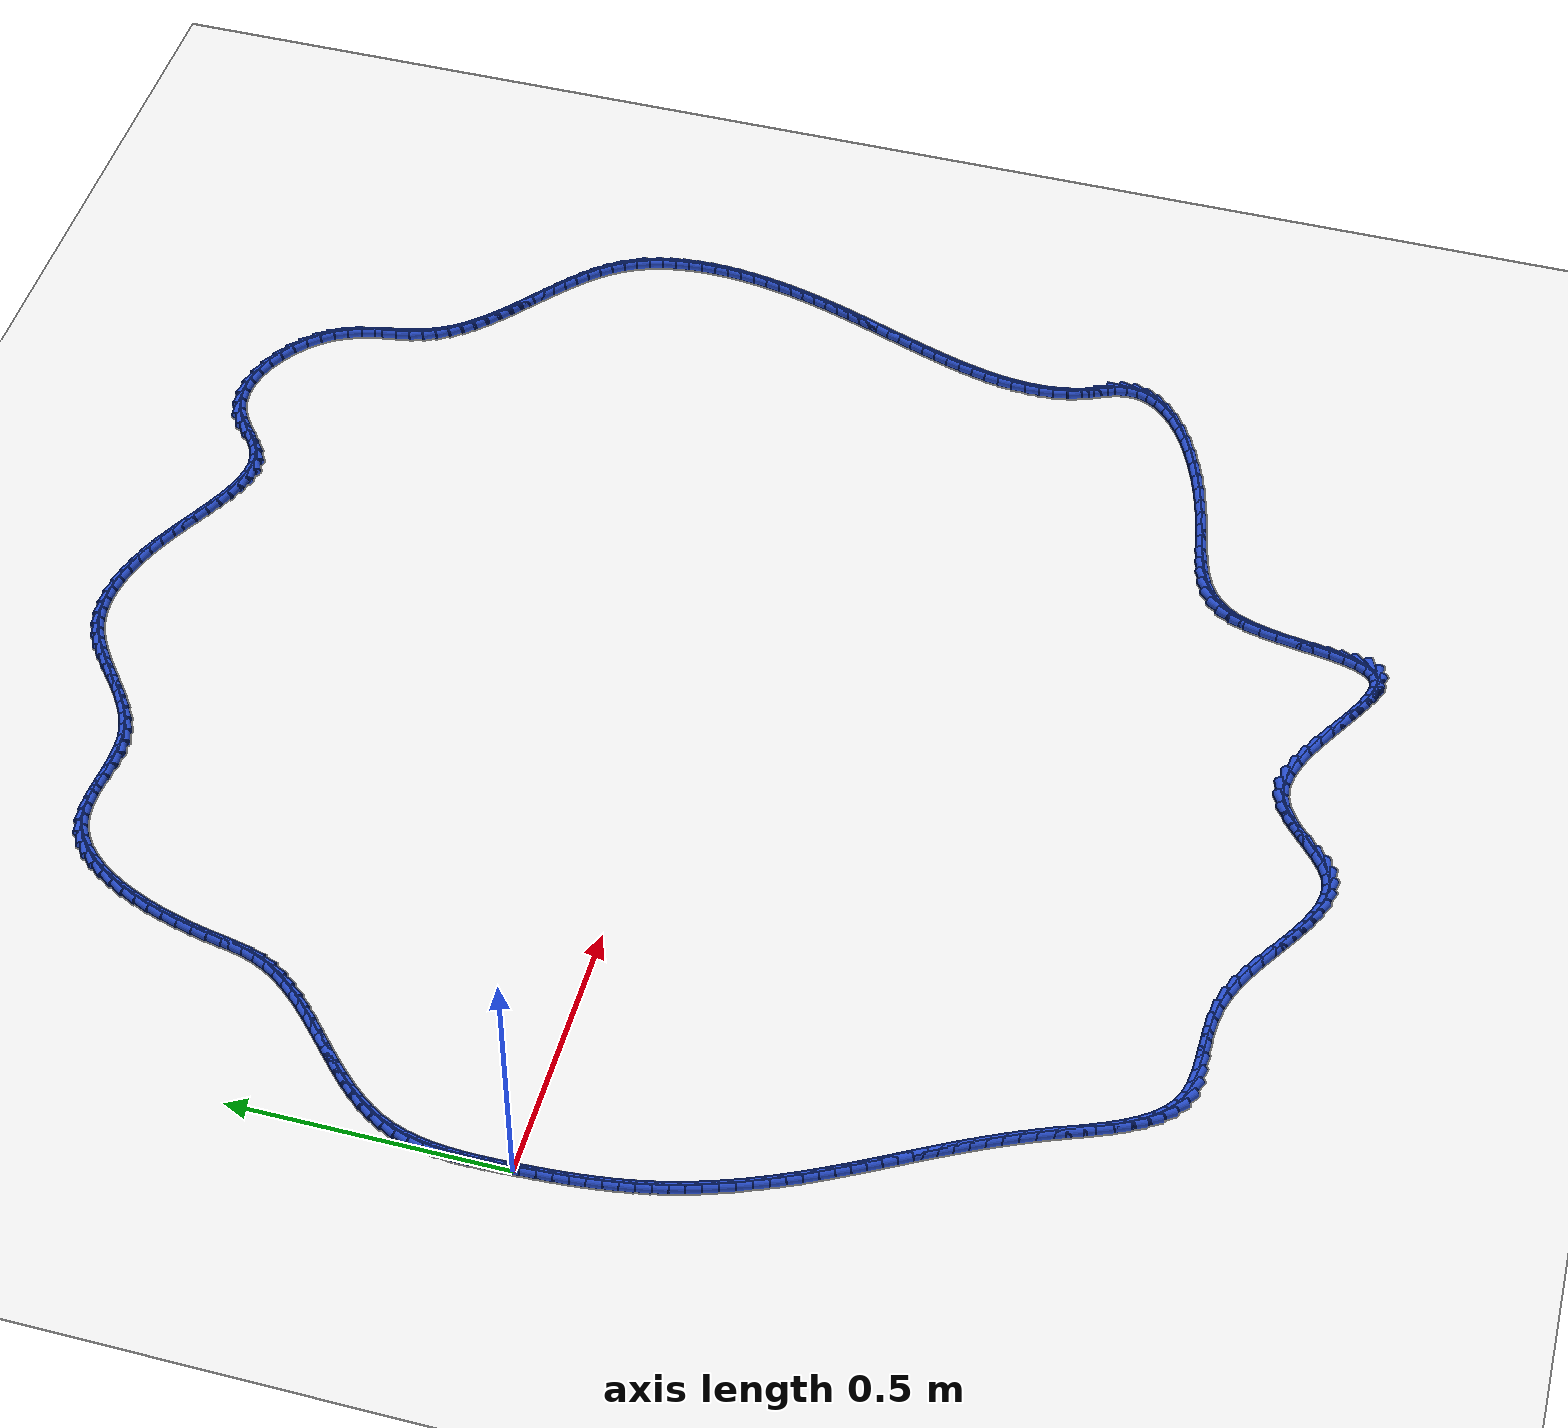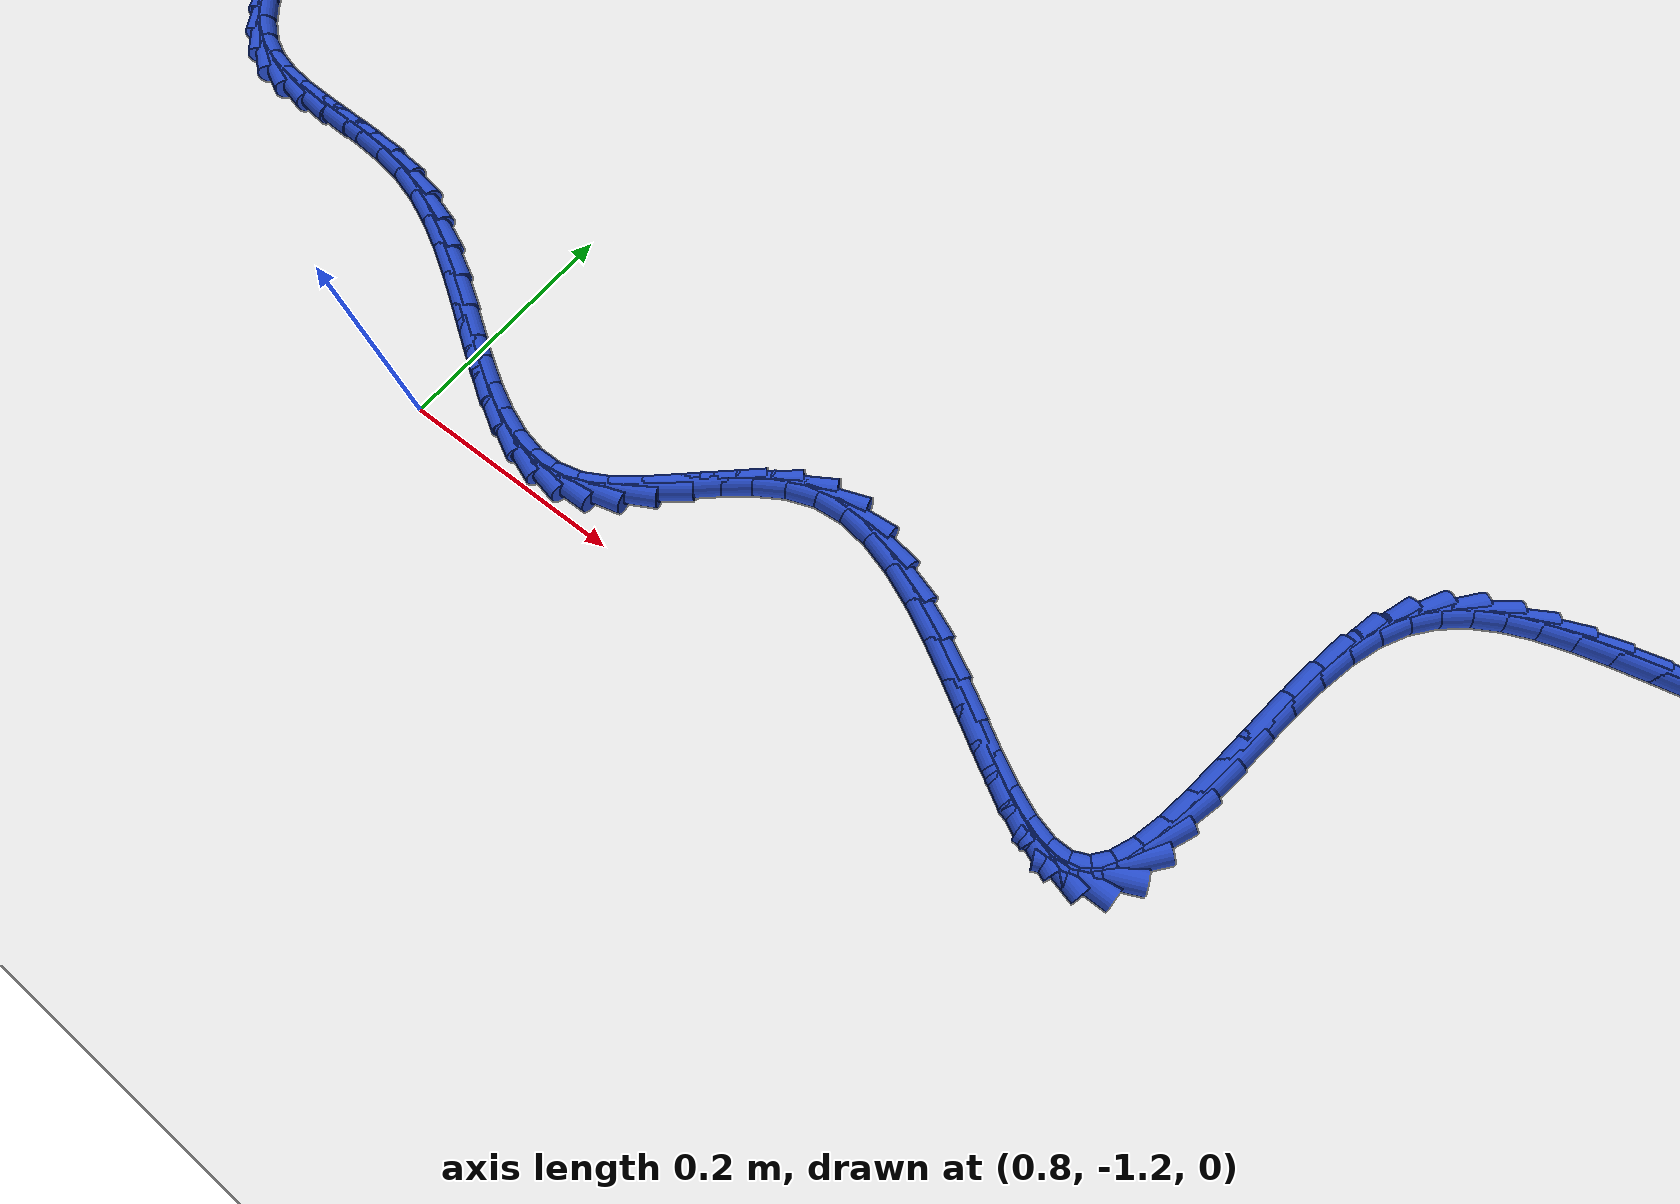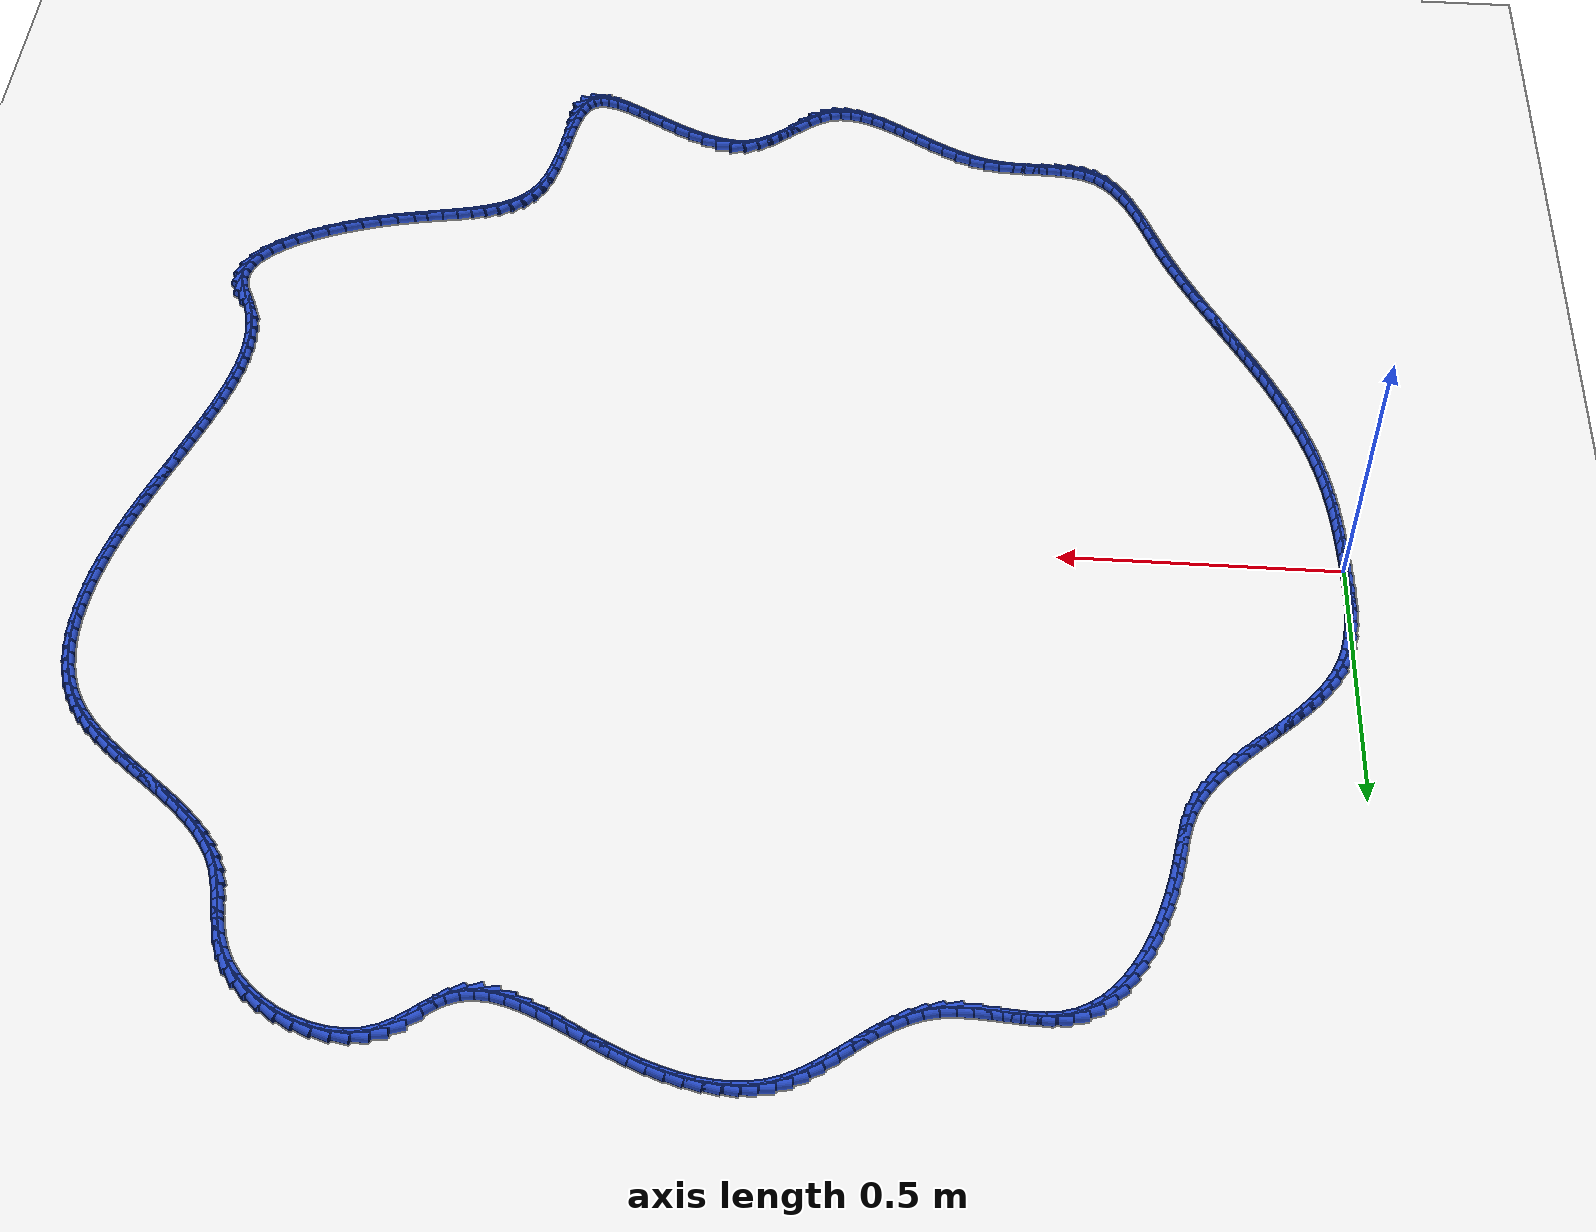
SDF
<sdf version="1.6">
 <world name="default">
  <light name="sun" type="directional">
   <pose>0 0 10 0 -0 0</pose>
   <diffuse>0.8 0.8 0.8 1</diffuse>
   <specular>0.2 0.2 0.2 1</specular>
   <attenuation>
    <range>1000</range>
    <constant>0.9</constant>
    <linear>0.01</linear>
    <quadratic>0.001</quadratic>
   </attenuation>
   <direction>-0.5 0.1 -0.9</direction>
  </light>
  <model name="ground_plane">
   <static>1</static>
   <link name="link">
    <collision name="collision">
     <geometry><plane><normal>0 0 1</normal><size>100 100</size></plane></geometry>
     <surface><friction><ode><mu>100</mu><mu2>50</mu2></ode></friction></surface>
    </collision>
    <visual name="visual">
     <cast_shadows>0</cast_shadows>
     <geometry><plane><normal>0 0 1</normal><size>100 100</size></plane></geometry>
     <material>
      <script><uri>file://media/materials/scripts/gazebo.material</uri><name>Gazebo/WhiteGlow</name></script>
     </material>
    </visual>
   </link>
  </model>
  <gravity>0 0 -9.8</gravity>
  <magnetic_field>6e-06 2.3e-05 -4.2e-05</magnetic_field>
  <atmosphere type="adiabatic"/>
  <physics name="default_physics" default="0" type="ode">
   <max_step_size>0.001</max_step_size>
   <real_time_factor>1</real_time_factor>
   <real_time_update_rate>1000</real_time_update_rate>
  </physics>
  <scene><ambient>0.4 0.4 0.4 1</ambient><background>0.7 0.7 0.7 1</background><shadows>1</shadows></scene>
  <spherical_coordinates>
   <surface_model>EARTH_WGS84</surface_model>
   <latitude_deg>0</latitude_deg>
   <longitude_deg>0</longitude_deg>
   <elevation>0</elevation>
   <heading_deg>0</heading_deg>
  </spherical_coordinates>
  <model name="line">
   <link name="link_0">
    <pose>1.734723475976807e-18 -2.0816681711721685e-17 0.01 0 1.57 -1.532886110411397</pose>
    <collision name="collision">
     <geometry><cylinder><radius>0.01</radius><length>0.08</length></cylinder></geometry>
    </collision>
    <visual name="visual">
     <material>
      <script><name>Gazebo/Blue</name><uri>file://media/materials/scripts/gazebo.material</uri></script>
     </material>
     <geometry><cylinder><radius>0.01</radius><length>0.08</length></cylinder></geometry>
    </visual>
   </link>
   <link name="link_1">
    <pose>-0.001054489585071092 0.02780211963542385 0.01 0 1.57 -1.550534901083931</pose>
    <collision name="collision">
     <geometry><cylinder><radius>0.01</radius><length>0.08</length></cylinder></geometry>
    </collision>
    <visual name="visual">
     <material>
      <script><name>Gazebo/Blue</name><uri>file://media/materials/scripts/gazebo.material</uri></script>
     </material>
     <geometry><cylinder><radius>0.01</radius><length>0.08</length></cylinder></geometry>
    </visual>
   </link>
   <link name="link_2">
    <pose>-0.0016200203628982863 0.05570999717233436 0.01 0 1.57 1.5635487329833877</pose>
    <collision name="collision">
     <geometry><cylinder><radius>0.01</radius><length>0.08</length></cylinder></geometry>
    </collision>
    <visual name="visual">
     <material>
      <script><name>Gazebo/Blue</name><uri>file://media/materials/scripts/gazebo.material</uri></script>
     </material>
     <geometry><cylinder><radius>0.01</radius><length>0.08</length></cylinder></geometry>
    </visual>
   </link>
   <link name="link_3">
    <pose>-0.0014181952436658097 0.08355669921876518 0.01 0 1.57 1.525655338502662</pose>
    <collision name="collision">
     <geometry><cylinder><radius>0.01</radius><length>0.08</length></cylinder></geometry>
    </collision>
    <visual name="visual">
     <material>
      <script><name>Gazebo/Blue</name><uri>file://media/materials/scripts/gazebo.material</uri></script>
     </material>
     <geometry><cylinder><radius>0.01</radius><length>0.08</length></cylinder></geometry>
    </visual>
   </link>
   <link name="link_4">
    <pose>-0.00017061713755789007 0.11117529238274991 0.01 0 1.57 1.4766088035250573</pose>
    <collision name="collision">
     <geometry><cylinder><radius>0.01</radius><length>0.08</length></cylinder></geometry>
    </collision>
    <visual name="visual">
     <material>
      <script><name>Gazebo/Blue</name><uri>file://media/materials/scripts/gazebo.material</uri></script>
     </material>
     <geometry><cylinder><radius>0.01</radius><length>0.08</length></cylinder></geometry>
    </visual>
   </link>
   <link name="link_5">
    <pose>0.0024011110452412422 0.13839884327232227 0.01 0 1.57 1.4154918935702672</pose>
    <collision name="collision">
     <geometry><cylinder><radius>0.01</radius><length>0.08</length></cylinder></geometry>
    </collision>
    <visual name="visual">
     <material>
      <script><name>Gazebo/Blue</name><uri>file://media/materials/scripts/gazebo.material</uri></script>
     </material>
     <geometry><cylinder><radius>0.01</radius><length>0.08</length></cylinder></geometry>
    </visual>
   </link>
   <link name="link_6">
    <pose>0.006575386394547364 0.16506041849551586 0.01 0 1.57 1.3414084571035907</pose>
    <collision name="collision">
     <geometry><cylinder><radius>0.01</radius><length>0.08</length></cylinder></geometry>
    </collision>
    <visual name="visual">
     <material>
      <script><name>Gazebo/Blue</name><uri>file://media/materials/scripts/gazebo.material</uri></script>
     </material>
     <geometry><cylinder><radius>0.01</radius><length>0.08</length></cylinder></geometry>
    </visual>
   </link>
   <link name="link_7">
    <pose>0.01263060600017624 0.19099308466036435 0.01 0 1.57 1.2537638976980172</pose>
    <collision name="collision">
     <geometry><cylinder><radius>0.01</radius><length>0.08</length></cylinder></geometry>
    </collision>
    <visual name="visual">
     <material>
      <script><name>Gazebo/Blue</name><uri>file://media/materials/scripts/gazebo.material</uri></script>
     </material>
     <geometry><cylinder><radius>0.01</radius><length>0.08</length></cylinder></geometry>
    </visual>
   </link>
   <link name="link_8">
    <pose>0.020845166951943644 0.21602990837490138 0.01 0 1.57 1.1529521189873344</pose>
    <collision name="collision">
     <geometry><cylinder><radius>0.01</radius><length>0.08</length></cylinder></geometry>
    </collision>
    <visual name="visual">
     <material>
      <script><name>Gazebo/Blue</name><uri>file://media/materials/scripts/gazebo.material</uri></script>
     </material>
     <geometry><cylinder><radius>0.01</radius><length>0.08</length></cylinder></geometry>
    </visual>
   </link>
   <link name="link_9">
    <pose>0.031490871609810706 0.24000729775779747 0.01 0 1.57 1.0513104828891866</pose>
    <collision name="collision">
     <geometry><cylinder><radius>0.01</radius><length>0.08</length></cylinder></geometry>
    </collision>
    <visual name="visual">
     <material>
      <script><name>Gazebo/Blue</name><uri>file://media/materials/scripts/gazebo.material</uri></script>
     </material>
     <geometry><cylinder><radius>0.01</radius><length>0.08</length></cylinder></geometry>
    </visual>
   </link>
   <link name="link_10">
    <pose>0.04457908712071924 0.26289362191076504 0.01 0 1.57 0.9647965593218606</pose>
    <collision name="collision">
     <geometry><cylinder><radius>0.01</radius><length>0.08</length></cylinder></geometry>
    </collision>
    <visual name="visual">
     <material>
      <script><name>Gazebo/Blue</name><uri>file://media/materials/scripts/gazebo.material</uri></script>
     </material>
     <geometry><cylinder><radius>0.01</radius><length>0.08</length></cylinder></geometry>
    </visual>
   </link>
   <link name="link_11">
    <pose>0.05978049539242175 0.2848298731324727 0.01 0 1.57 0.8945799264818539</pose>
    <collision name="collision">
     <geometry><cylinder><radius>0.01</radius><length>0.08</length></cylinder></geometry>
    </collision>
    <visual name="visual">
     <material>
      <script><name>Gazebo/Blue</name><uri>file://media/materials/scripts/gazebo.material</uri></script>
     </material>
     <geometry><cylinder><radius>0.01</radius><length>0.08</length></cylinder></geometry>
    </visual>
   </link>
   <link name="link_12">
    <pose>0.07674276971952632 0.30596870204986837 0.01 0 1.57 0.8399753419119388</pose>
    <collision name="collision">
     <geometry><cylinder><radius>0.01</radius><length>0.08</length></cylinder></geometry>
    </collision>
    <visual name="visual">
     <material>
      <script><name>Gazebo/Blue</name><uri>file://media/materials/scripts/gazebo.material</uri></script>
     </material>
     <geometry><cylinder><radius>0.01</radius><length>0.08</length></cylinder></geometry>
    </visual>
   </link>
   <link name="link_13">
    <pose>0.09511358339664111 0.32646275928990004 0.01 0 1.57 0.7999780329652985</pose>
    <collision name="collision">
     <geometry><cylinder><radius>0.01</radius><length>0.08</length></cylinder></geometry>
    </collision>
    <visual name="visual">
     <material>
      <script><name>Gazebo/Blue</name><uri>file://media/materials/scripts/gazebo.material</uri></script>
     </material>
     <geometry><cylinder><radius>0.01</radius><length>0.08</length></cylinder></geometry>
    </visual>
   </link>
   <link name="link_14">
    <pose>0.1145406097183744 0.34646469547951625 0.01 0 1.57 0.7736267360686331</pose>
    <collision name="collision">
     <geometry><cylinder><radius>0.01</radius><length>0.08</length></cylinder></geometry>
    </collision>
    <visual name="visual">
     <material>
      <script><name>Gazebo/Blue</name><uri>file://media/materials/scripts/gazebo.material</uri></script>
     </material>
     <geometry><cylinder><radius>0.01</radius><length>0.08</length></cylinder></geometry>
    </visual>
   </link>
   <link name="link_15">
    <pose>0.13467152197933413 0.36612716124566463 0.01 0 1.57 0.760206472804146</pose>
    <collision name="collision">
     <geometry><cylinder><radius>0.01</radius><length>0.08</length></cylinder></geometry>
    </collision>
    <visual name="visual">
     <material>
      <script><name>Gazebo/Blue</name><uri>file://media/materials/scripts/gazebo.material</uri></script>
     </material>
     <geometry><cylinder><radius>0.01</radius><length>0.08</length></cylinder></geometry>
    </visual>
   </link>
   <link name="link_16">
    <pose>0.15515399347412867 0.3856028072152936 0.01 0 1.57 0.7593483373574004</pose>
    <collision name="collision">
     <geometry><cylinder><radius>0.01</radius><length>0.08</length></cylinder></geometry>
    </collision>
    <visual name="visual">
     <material>
      <script><name>Gazebo/Blue</name><uri>file://media/materials/scripts/gazebo.material</uri></script>
     </material>
     <geometry><cylinder><radius>0.01</radius><length>0.08</length></cylinder></geometry>
    </visual>
   </link>
   <link name="link_17">
    <pose>0.17563569749736607 0.40504428401535125 0.01 0 1.57 0.771071300309756</pose>
    <collision name="collision">
     <geometry><cylinder><radius>0.01</radius><length>0.08</length></cylinder></geometry>
    </collision>
    <visual name="visual">
     <material>
      <script><name>Gazebo/Blue</name><uri>file://media/materials/scripts/gazebo.material</uri></script>
     </material>
     <geometry><cylinder><radius>0.01</radius><length>0.08</length></cylinder></geometry>
    </visual>
   </link>
   <link name="link_18">
    <pose>0.19576430734365435 0.42460424227278526 0.01 0 1.57 0.7957890482763234</pose>
    <collision name="collision">
     <geometry><cylinder><radius>0.01</radius><length>0.08</length></cylinder></geometry>
    </collision>
    <visual name="visual">
     <material>
      <script><name>Gazebo/Blue</name><uri>file://media/materials/scripts/gazebo.material</uri></script>
     </material>
     <geometry><cylinder><radius>0.01</radius><length>0.08</length></cylinder></geometry>
    </visual>
   </link>
   <link name="link_19">
    <pose>0.21518749630760192 0.4444353326145443 0.01 0 1.57 0.8342824467986034</pose>
    <collision name="collision">
     <geometry><cylinder><radius>0.01</radius><length>0.08</length></cylinder></geometry>
    </collision>
    <visual name="visual">
     <material>
      <script><name>Gazebo/Blue</name><uri>file://media/materials/scripts/gazebo.material</uri></script>
     </material>
     <geometry><cylinder><radius>0.01</radius><length>0.08</length></cylinder></geometry>
    </visual>
   </link>
   <link name="link_20">
    <pose>0.23355293768381674 0.4646902056675761 0.01 0 1.57 0.8876149132541281</pose>
    <collision name="collision">
     <geometry><cylinder><radius>0.01</radius><length>0.08</length></cylinder></geometry>
    </collision>
    <visual name="visual">
     <material>
      <script><name>Gazebo/Blue</name><uri>file://media/materials/scripts/gazebo.material</uri></script>
     </material>
     <geometry><cylinder><radius>0.01</radius><length>0.08</length></cylinder></geometry>
    </visual>
   </link>
   <link name="link_21">
    <pose>0.2505083047669071 0.485521512058829 0.01 0 1.57 0.9569428256014516</pose>
    <collision name="collision">
     <geometry><cylinder><radius>0.01</radius><length>0.08</length></cylinder></geometry>
    </collision>
    <visual name="visual">
     <material>
      <script><name>Gazebo/Blue</name><uri>file://media/materials/scripts/gazebo.material</uri></script>
     </material>
     <geometry><cylinder><radius>0.01</radius><length>0.08</length></cylinder></geometry>
    </visual>
   </link>
   <link name="link_22">
    <pose>0.2657012708514811 0.5070819024152509 0.01 0 1.57 1.0431542261373234</pose>
    <collision name="collision">
     <geometry><cylinder><radius>0.01</radius><length>0.08</length></cylinder></geometry>
    </collision>
    <visual name="visual">
     <material>
      <script><name>Gazebo/Blue</name><uri>file://media/materials/scripts/gazebo.material</uri></script>
     </material>
     <geometry><cylinder><radius>0.01</radius><length>0.08</length></cylinder></geometry>
    </visual>
   </link>
   <link name="link_23">
    <pose>0.2787795092321467 0.5295240273637899 0.01 0 1.57 1.1462874696964127</pose>
    <collision name="collision">
     <geometry><cylinder><radius>0.01</radius><length>0.08</length></cylinder></geometry>
    </collision>
    <visual name="visual">
     <material>
      <script><name>Gazebo/Blue</name><uri>file://media/materials/scripts/gazebo.material</uri></script>
     </material>
     <geometry><cylinder><radius>0.01</radius><length>0.08</length></cylinder></geometry>
    </visual>
   </link>
   <link name="link_24">
    <pose>0.28939069320351246 0.5530005375313943 0.01 0 1.57 1.2573030293908356</pose>
    <collision name="collision">
     <geometry><cylinder><radius>0.01</radius><length>0.08</length></cylinder></geometry>
    </collision>
    <visual name="visual">
     <material>
      <script><name>Gazebo/Blue</name><uri>file://media/materials/scripts/gazebo.material</uri></script>
     </material>
     <geometry><cylinder><radius>0.01</radius><length>0.08</length></cylinder></geometry>
    </visual>
   </link>
   <link name="link_25">
    <pose>0.2973763518225376 0.5776336748269737 0.01 0 1.57 1.3383966498846531</pose>
    <collision name="collision">
     <geometry><cylinder><radius>0.01</radius><length>0.08</length></cylinder></geometry>
    </collision>
    <visual name="visual">
     <material>
      <script><name>Gazebo/Blue</name><uri>file://media/materials/scripts/gazebo.material</uri></script>
     </material>
     <geometry><cylinder><radius>0.01</radius><length>0.08</length></cylinder></geometry>
    </visual>
   </link>
   <link name="link_26">
    <pose>0.3034757726418987 0.6034048564316531 0.01 0 1.57 1.3790585587075286</pose>
    <collision name="collision">
     <geometry><cylinder><radius>0.01</radius><length>0.08</length></cylinder></geometry>
    </collision>
    <visual name="visual">
     <material>
      <script><name>Gazebo/Blue</name><uri>file://media/materials/scripts/gazebo.material</uri></script>
     </material>
     <geometry><cylinder><radius>0.01</radius><length>0.08</length></cylinder></geometry>
    </visual>
   </link>
   <link name="link_27">
    <pose>0.30868794308638425 0.6302547623305625 0.01 0 1.57 1.3820387423248808</pose>
    <collision name="collision">
     <geometry><cylinder><radius>0.01</radius><length>0.08</length></cylinder></geometry>
    </collision>
    <visual name="visual">
     <material>
      <script><name>Gazebo/Blue</name><uri>file://media/materials/scripts/gazebo.material</uri></script>
     </material>
     <geometry><cylinder><radius>0.01</radius><length>0.08</length></cylinder></geometry>
    </visual>
   </link>
   <link name="link_28">
    <pose>0.31401186530222835 0.6581240641139906 0.01 0 1.57 1.3565869018099266</pose>
    <collision name="collision">
     <geometry><cylinder><radius>0.01</radius><length>0.08</length></cylinder></geometry>
    </collision>
    <visual name="visual">
     <material>
      <script><name>Gazebo/Blue</name><uri>file://media/materials/scripts/gazebo.material</uri></script>
     </material>
     <geometry><cylinder><radius>0.01</radius><length>0.08</length></cylinder></geometry>
    </visual>
   </link>
   <link name="link_29">
    <pose>0.3202690441799271 0.6868864767038024 0.01 0 1.57 1.3238237011585037</pose>
    <collision name="collision">
     <geometry><cylinder><radius>0.01</radius><length>0.08</length></cylinder></geometry>
    </collision>
    <visual name="visual">
     <material>
      <script><name>Gazebo/Blue</name><uri>file://media/materials/scripts/gazebo.material</uri></script>
     </material>
     <geometry><cylinder><radius>0.01</radius><length>0.08</length></cylinder></geometry>
    </visual>
   </link>
   <link name="link_30">
    <pose>0.32765434823906264 0.7161793311773075 0.01 0 1.57 1.287233978818466</pose>
    <collision name="collision">
     <geometry><cylinder><radius>0.01</radius><length>0.08</length></cylinder></geometry>
    </collision>
    <visual name="visual">
     <material>
      <script><name>Gazebo/Blue</name><uri>file://media/materials/scripts/gazebo.material</uri></script>
     </material>
     <geometry><cylinder><radius>0.01</radius><length>0.08</length></cylinder></geometry>
    </visual>
   </link>
   <link name="link_31">
    <pose>0.336224428931923 0.745587819471371 0.01 0 1.57 1.2456978939927081</pose>
    <collision name="collision">
     <geometry><cylinder><radius>0.01</radius><length>0.08</length></cylinder></geometry>
    </collision>
    <visual name="visual">
     <material>
      <script><name>Gazebo/Blue</name><uri>file://media/materials/scripts/gazebo.material</uri></script>
     </material>
     <geometry><cylinder><radius>0.01</radius><length>0.08</length></cylinder></geometry>
    </visual>
   </link>
   <link name="link_32">
    <pose>0.3460359377107962 0.7746971335228588 0.01 0 1.57 1.1978583400434655</pose>
    <collision name="collision">
     <geometry><cylinder><radius>0.01</radius><length>0.08</length></cylinder></geometry>
    </collision>
    <visual name="visual">
     <material>
      <script><name>Gazebo/Blue</name><uri>file://media/materials/scripts/gazebo.material</uri></script>
     </material>
     <geometry><cylinder><radius>0.01</radius><length>0.08</length></cylinder></geometry>
    </visual>
   </link>
   <link name="link_33">
    <pose>0.35714552602797056 0.8030924652686364 0.01 0 1.57 1.142029988332654</pose>
    <collision name="collision">
     <geometry><cylinder><radius>0.01</radius><length>0.08</length></cylinder></geometry>
    </collision>
    <visual name="visual">
     <material>
      <script><name>Gazebo/Blue</name><uri>file://media/materials/scripts/gazebo.material</uri></script>
     </material>
     <geometry><cylinder><radius>0.01</radius><length>0.08</length></cylinder></geometry>
    </visual>
   </link>
   <link name="link_34">
    <pose>0.36960984533573404 0.8303590066455696 0.01 0 1.57 1.0761052453301645</pose>
    <collision name="collision">
     <geometry><cylinder><radius>0.01</radius><length>0.08</length></cylinder></geometry>
    </collision>
    <visual name="visual">
     <material>
      <script><name>Gazebo/Blue</name><uri>file://media/materials/scripts/gazebo.material</uri></script>
     </material>
     <geometry><cylinder><radius>0.01</radius><length>0.08</length></cylinder></geometry>
    </visual>
   </link>
   <link name="link_35">
    <pose>0.3834855470863747 0.8560819495905233 0.01 0 1.57 0.9974803519455353</pose>
    <collision name="collision">
     <geometry><cylinder><radius>0.01</radius><length>0.08</length></cylinder></geometry>
    </collision>
    <visual name="visual">
     <material>
      <script><name>Gazebo/Blue</name><uri>file://media/materials/scripts/gazebo.material</uri></script>
     </material>
     <geometry><cylinder><radius>0.01</radius><length>0.08</length></cylinder></geometry>
    </visual>
   </link>
   <link name="link_36">
    <pose>0.3988292827321809 0.879846486040364 0.01 0 1.57 0.9030677132607141</pose>
    <collision name="collision">
     <geometry><cylinder><radius>0.01</radius><length>0.08</length></cylinder></geometry>
    </collision>
    <visual name="visual">
     <material>
      <script><name>Gazebo/Blue</name><uri>file://media/materials/scripts/gazebo.material</uri></script>
     </material>
     <geometry><cylinder><radius>0.01</radius><length>0.08</length></cylinder></geometry>
    </visual>
   </link>
   <link name="link_37">
    <pose>0.4156977037254406 0.9012378079319568 0.01 0 1.57 0.7895419671899593</pose>
    <collision name="collision">
     <geometry><cylinder><radius>0.01</radius><length>0.08</length></cylinder></geometry>
    </collision>
    <visual name="visual">
     <material>
      <script><name>Gazebo/Blue</name><uri>file://media/materials/scripts/gazebo.material</uri></script>
     </material>
     <geometry><cylinder><radius>0.01</radius><length>0.08</length></cylinder></geometry>
    </visual>
   </link>
   <link name="link_38">
    <pose>0.43414746151844197 0.9198411072021677 0.01 0 1.57 0.6540784379596216</pose>
    <collision name="collision">
     <geometry><cylinder><radius>0.01</radius><length>0.08</length></cylinder></geometry>
    </collision>
    <visual name="visual">
     <material>
      <script><name>Gazebo/Blue</name><uri>file://media/materials/scripts/gazebo.material</uri></script>
     </material>
     <geometry><cylinder><radius>0.01</radius><length>0.08</length></cylinder></geometry>
    </visual>
   </link>
   <link name="link_39">
    <pose>0.4542352075634731 0.9352415757878618 0.01 0 1.57 0.4958560009905526</pose>
    <collision name="collision">
     <geometry><cylinder><radius>0.01</radius><length>0.08</length></cylinder></geometry>
    </collision>
    <visual name="visual">
     <material>
      <script><name>Gazebo/Blue</name><uri>file://media/materials/scripts/gazebo.material</uri></script>
     </material>
     <geometry><cylinder><radius>0.01</radius><length>0.08</length></cylinder></geometry>
    </visual>
   </link>
   <link name="link_40">
    <pose>0.476017593312822 0.9470244056259052 0.01 0 1.57 0.31815796675706753</pose>
    <collision name="collision">
     <geometry><cylinder><radius>0.01</radius><length>0.08</length></cylinder></geometry>
    </collision>
    <visual name="visual">
     <material>
      <script><name>Gazebo/Blue</name><uri>file://media/materials/scripts/gazebo.material</uri></script>
     </material>
     <geometry><cylinder><radius>0.01</radius><length>0.08</length></cylinder></geometry>
    </visual>
   </link>
   <link name="link_41">
    <pose>0.499551174423336 0.9547751041185908 0.01 0 1.57 0.14423825000075716</pose>
    <collision name="collision">
     <geometry><cylinder><radius>0.01</radius><length>0.08</length></cylinder></geometry>
    </collision>
    <visual name="visual">
     <material>
      <script><name>Gazebo/Blue</name><uri>file://media/materials/scripts/gazebo.material</uri></script>
     </material>
     <geometry><cylinder><radius>0.01</radius><length>0.08</length></cylinder></geometry>
    </visual>
   </link>
   <link name="link_42">
    <pose>0.5247829555773309 0.9584399426525169 0.01 0 1.57 0.021829071699389333</pose>
    <collision name="collision">
     <geometry><cylinder><radius>0.01</radius><length>0.08</length></cylinder></geometry>
    </collision>
    <visual name="visual">
     <material>
      <script><name>Gazebo/Blue</name><uri>file://media/materials/scripts/gazebo.material</uri></script>
     </material>
     <geometry><cylinder><radius>0.01</radius><length>0.08</length></cylinder></geometry>
    </visual>
   </link>
   <link name="link_43">
    <pose>0.5513397123114506 0.9590197440957087 0.01 0 1.57 -0.04778637897986153</pose>
    <collision name="collision">
     <geometry><cylinder><radius>0.01</radius><length>0.08</length></cylinder></geometry>
    </collision>
    <visual name="visual">
     <material>
      <script><name>Gazebo/Blue</name><uri>file://media/materials/scripts/gazebo.material</uri></script>
     </material>
     <geometry><cylinder><radius>0.01</radius><length>0.08</length></cylinder></geometry>
    </visual>
   </link>
   <link name="link_44">
    <pose>0.5787900191554317 0.9577069939392998 0.01 0 1.57 -0.07198721304770839</pose>
    <collision name="collision">
     <geometry><cylinder><radius>0.01</radius><length>0.08</length></cylinder></geometry>
    </collision>
    <visual name="visual">
     <material>
      <script><name>Gazebo/Blue</name><uri>file://media/materials/scripts/gazebo.material</uri></script>
     </material>
     <geometry><cylinder><radius>0.01</radius><length>0.08</length></cylinder></geometry>
    </visual>
   </link>
   <link name="link_45">
    <pose>0.6067024506390097 0.9556941776744233 0.01 0 1.57 -0.054356800121898474</pose>
    <collision name="collision">
     <geometry><cylinder><radius>0.01</radius><length>0.08</length></cylinder></geometry>
    </collision>
    <visual name="visual">
     <material>
      <script><name>Gazebo/Blue</name><uri>file://media/materials/scripts/gazebo.material</uri></script>
     </material>
     <geometry><cylinder><radius>0.01</radius><length>0.08</length></cylinder></geometry>
    </visual>
   </link>
   <link name="link_46">
    <pose>0.6346455812919212 0.9541737807922133 0.01 0 1.57 0.005972827688766767</pose>
    <collision name="collision">
     <geometry><cylinder><radius>0.01</radius><length>0.08</length></cylinder></geometry>
    </collision>
    <visual name="visual">
     <material>
      <script><name>Gazebo/Blue</name><uri>file://media/materials/scripts/gazebo.material</uri></script>
     </material>
     <geometry><cylinder><radius>0.01</radius><length>0.08</length></cylinder></geometry>
    </visual>
   </link>
   <link name="link_47">
    <pose>0.6621879856439024 0.9543382887838028 0.01 0 1.57 0.11339648721736466</pose>
    <collision name="collision">
     <geometry><cylinder><radius>0.01</radius><length>0.08</length></cylinder></geometry>
    </collision>
    <visual name="visual">
     <material>
      <script><name>Gazebo/Blue</name><uri>file://media/materials/scripts/gazebo.material</uri></script>
     </material>
     <geometry><cylinder><radius>0.01</radius><length>0.08</length></cylinder></geometry>
    </visual>
   </link>
   <link name="link_48">
    <pose>0.6888982382246888 0.9573801871403254 0.01 0 1.57 0.26552585125540934</pose>
    <collision name="collision">
     <geometry><cylinder><radius>0.01</radius><length>0.08</length></cylinder></geometry>
    </collision>
    <visual name="visual">
     <material>
      <script><name>Gazebo/Blue</name><uri>file://media/materials/scripts/gazebo.material</uri></script>
     </material>
     <geometry><cylinder><radius>0.01</radius><length>0.08</length></cylinder></geometry>
    </visual>
   </link>
   <link name="link_49">
    <pose>0.7144036866667239 0.9643163227979136 0.01 0 1.57 0.4104750478282897</pose>
    <collision name="collision">
     <geometry><cylinder><radius>0.01</radius><length>0.08</length></cylinder></geometry>
    </collision>
    <visual name="visual">
     <material>
      <script><name>Gazebo/Blue</name><uri>file://media/materials/scripts/gazebo.material</uri></script>
     </material>
     <geometry><cylinder><radius>0.01</radius><length>0.08</length></cylinder></geometry>
    </visual>
   </link>
   <link name="link_50">
    <pose>0.7387504907703724 0.9749119571781819 0.01 0 1.57 0.5222467683999191</pose>
    <collision name="collision">
     <geometry><cylinder><radius>0.01</radius><length>0.08</length></cylinder></geometry>
    </collision>
    <visual name="visual">
     <material>
      <script><name>Gazebo/Blue</name><uri>file://media/materials/scripts/gazebo.material</uri></script>
     </material>
     <geometry><cylinder><radius>0.01</radius><length>0.08</length></cylinder></geometry>
    </visual>
   </link>
   <link name="link_51">
    <pose>0.7621666036343023 0.9883890774709587 0.01 0 1.57 0.6011634717574081</pose>
    <collision name="collision">
     <geometry><cylinder><radius>0.01</radius><length>0.08</length></cylinder></geometry>
    </collision>
    <visual name="visual">
     <material>
      <script><name>Gazebo/Blue</name><uri>file://media/materials/scripts/gazebo.material</uri></script>
     </material>
     <geometry><cylinder><radius>0.01</radius><length>0.08</length></cylinder></geometry>
    </visual>
   </link>
   <link name="link_52">
    <pose>0.7848807163912173 1.003967465312415 0.01 0 1.57 0.6497685850245833</pose>
    <collision name="collision">
     <geometry><cylinder><radius>0.01</radius><length>0.08</length></cylinder></geometry>
    </collision>
    <visual name="visual">
     <material>
      <script><name>Gazebo/Blue</name><uri>file://media/materials/scripts/gazebo.material</uri></script>
     </material>
     <geometry><cylinder><radius>0.01</radius><length>0.08</length></cylinder></geometry>
    </visual>
   </link>
   <link name="link_53">
    <pose>0.8071215201738202 1.0208669023387216 0.01 0 1.57 0.6703824752988023</pose>
    <collision name="collision">
     <geometry><cylinder><radius>0.01</radius><length>0.08</length></cylinder></geometry>
    </collision>
    <visual name="visual">
     <material>
      <script><name>Gazebo/Blue</name><uri>file://media/materials/scripts/gazebo.material</uri></script>
     </material>
     <geometry><cylinder><radius>0.01</radius><length>0.08</length></cylinder></geometry>
    </visual>
   </link>
   <link name="link_54">
    <pose>0.8291177061148156 1.0383071701860493 0.01 0 1.57 0.6640162065978206</pose>
    <collision name="collision">
     <geometry><cylinder><radius>0.01</radius><length>0.08</length></cylinder></geometry>
    </collision>
    <visual name="visual">
     <material>
      <script><name>Gazebo/Blue</name><uri>file://media/materials/scripts/gazebo.material</uri></script>
     </material>
     <geometry><cylinder><radius>0.01</radius><length>0.08</length></cylinder></geometry>
    </visual>
   </link>
   <link name="link_55">
    <pose>0.8510979653469058 1.0555080504905685 0.01 0 1.57 0.6300004108136756</pose>
    <collision name="collision">
     <geometry><cylinder><radius>0.01</radius><length>0.08</length></cylinder></geometry>
    </collision>
    <visual name="visual">
     <material>
      <script><name>Gazebo/Blue</name><uri>file://media/materials/scripts/gazebo.material</uri></script>
     </material>
     <geometry><cylinder><radius>0.01</radius><length>0.08</length></cylinder></geometry>
    </visual>
   </link>
   <link name="link_56">
    <pose>0.8732909890027951 1.0716893248884503 0.01 0 1.57 0.5660273629535294</pose>
    <collision name="collision">
     <geometry><cylinder><radius>0.01</radius><length>0.08</length></cylinder></geometry>
    </collision>
    <visual name="visual">
     <material>
      <script><name>Gazebo/Blue</name><uri>file://media/materials/scripts/gazebo.material</uri></script>
     </material>
     <geometry><cylinder><radius>0.01</radius><length>0.08</length></cylinder></geometry>
    </visual>
   </link>
   <link name="link_57">
    <pose>0.8959254682151868 1.0860707750158654 0.01 0 1.57 0.46875261034569793</pose>
    <collision name="collision">
     <geometry><cylinder><radius>0.01</radius><length>0.08</length></cylinder></geometry>
    </collision>
    <visual name="visual">
     <material>
      <script><name>Gazebo/Blue</name><uri>file://media/materials/scripts/gazebo.material</uri></script>
     </material>
     <geometry><cylinder><radius>0.01</radius><length>0.08</length></cylinder></geometry>
    </visual>
   </link>
   <link name="link_58">
    <pose>0.9192300941167846 1.0978721825089846 0.01 0 1.57 0.3392665636153728</pose>
    <collision name="collision">
     <geometry><cylinder><radius>0.01</radius><length>0.08</length></cylinder></geometry>
    </collision>
    <visual name="visual">
     <material>
      <script><name>Gazebo/Blue</name><uri>file://media/materials/scripts/gazebo.material</uri></script>
     </material>
     <geometry><cylinder><radius>0.01</radius><length>0.08</length></cylinder></geometry>
    </visual>
   </link>
   <link name="link_59">
    <pose>0.9434034261198739 1.1064032385717384 0.01 0 1.57 0.20520890322017646</pose>
    <collision name="collision">
     <geometry><cylinder><radius>0.01</radius><length>0.08</length></cylinder></geometry>
    </collision>
    <visual name="visual">
     <material>
      <script><name>Gazebo/Blue</name><uri>file://media/materials/scripts/gazebo.material</uri></script>
     </material>
     <geometry><cylinder><radius>0.01</radius><length>0.08</length></cylinder></geometry>
    </visual>
   </link>
   <link name="link_60">
    <pose>0.9684300054919652 1.1116122397921055 0.01 0 1.57 0.08175382094094812</pose>
    <collision name="collision">
     <geometry><cylinder><radius>0.01</radius><length>0.08</length></cylinder></geometry>
    </collision>
    <visual name="visual">
     <material>
      <script><name>Gazebo/Blue</name><uri>file://media/materials/scripts/gazebo.material</uri></script>
     </material>
     <geometry><cylinder><radius>0.01</radius><length>0.08</length></cylinder></geometry>
    </visual>
   </link>
   <link name="link_61">
    <pose>0.9942017420305705 1.1137238843479162 0.01 0 1.57 -0.02876723976940855</pose>
    <collision name="collision">
     <geometry><cylinder><radius>0.01</radius><length>0.08</length></cylinder></geometry>
    </collision>
    <visual name="visual">
     <material>
      <script><name>Gazebo/Blue</name><uri>file://media/materials/scripts/gazebo.material</uri></script>
     </material>
     <geometry><cylinder><radius>0.01</radius><length>0.08</length></cylinder></geometry>
    </visual>
   </link>
   <link name="link_62">
    <pose>1.0206101746797078 1.1129639770009223 0.01 0 1.57 -0.12576463096252255</pose>
    <collision name="collision">
     <geometry><cylinder><radius>0.01</radius><length>0.08</length></cylinder></geometry>
    </collision>
    <visual name="visual">
     <material>
      <script><name>Gazebo/Blue</name><uri>file://media/materials/scripts/gazebo.material</uri></script>
     </material>
     <geometry><cylinder><radius>0.01</radius><length>0.08</length></cylinder></geometry>
    </visual>
   </link>
   <link name="link_63">
    <pose>1.0475468423833965 1.1095583225128758 0.01 0 1.57 -0.20981740107546082</pose>
    <collision name="collision">
     <geometry><cylinder><radius>0.01</radius><length>0.08</length></cylinder></geometry>
    </collision>
    <visual name="visual">
     <material>
      <script><name>Gazebo/Blue</name><uri>file://media/materials/scripts/gazebo.material</uri></script>
     </material>
     <geometry><cylinder><radius>0.01</radius><length>0.08</length></cylinder></geometry>
    </visual>
   </link>
   <link name="link_64">
    <pose>1.0749032840856532 1.1037327256455274 0.01 0 1.57 -0.28212691487153047</pose>
    <collision name="collision">
     <geometry><cylinder><radius>0.01</radius><length>0.08</length></cylinder></geometry>
    </collision>
    <visual name="visual">
     <material>
      <script><name>Gazebo/Blue</name><uri>file://media/materials/scripts/gazebo.material</uri></script>
     </material>
     <geometry><cylinder><radius>0.01</radius><length>0.08</length></cylinder></geometry>
    </visual>
   </link>
   <link name="link_65">
    <pose>1.1025710387304979 1.0957129911606298 0.01 0 1.57 -0.344114325534344</pose>
    <collision name="collision">
     <geometry><cylinder><radius>0.01</radius><length>0.08</length></cylinder></geometry>
    </collision>
    <visual name="visual">
     <material>
      <script><name>Gazebo/Blue</name><uri>file://media/materials/scripts/gazebo.material</uri></script>
     </material>
     <geometry><cylinder><radius>0.01</radius><length>0.08</length></cylinder></geometry>
    </visual>
   </link>
   <link name="link_66">
    <pose>1.1304416452619481 1.0857249238199342 0.01 0 1.57 -0.39718096718352325</pose>
    <collision name="collision">
     <geometry><cylinder><radius>0.01</radius><length>0.08</length></cylinder></geometry>
    </collision>
    <visual name="visual">
     <material>
      <script><name>Gazebo/Blue</name><uri>file://media/materials/scripts/gazebo.material</uri></script>
     </material>
     <geometry><cylinder><radius>0.01</radius><length>0.08</length></cylinder></geometry>
    </visual>
   </link>
   <link name="link_67">
    <pose>1.1584066426240216 1.0739943283851923 0.01 0 1.57 -0.44253943432295173</pose>
    <collision name="collision">
     <geometry><cylinder><radius>0.01</radius><length>0.08</length></cylinder></geometry>
    </collision>
    <visual name="visual">
     <material>
      <script><name>Gazebo/Blue</name><uri>file://media/materials/scripts/gazebo.material</uri></script>
     </material>
     <geometry><cylinder><radius>0.01</radius><length>0.08</length></cylinder></geometry>
    </visual>
   </link>
   <link name="link_68">
    <pose>1.1863576080384484 1.0607487430096347 0.01 0 1.57 -0.4763200293725778</pose>
    <collision name="collision">
     <geometry><cylinder><radius>0.01</radius><length>0.08</length></cylinder></geometry>
    </collision>
    <visual name="visual">
     <material>
      <script><name>Gazebo/Blue</name><uri>file://media/materials/scripts/gazebo.material</uri></script>
     </material>
     <geometry><cylinder><radius>0.01</radius><length>0.08</length></cylinder></geometry>
    </visual>
   </link>
   <link name="link_69">
    <pose>1.2141899424522498 1.046388861783118 0.01 0 1.57 -0.49070860290854984</pose>
    <collision name="collision">
     <geometry><cylinder><radius>0.01</radius><length>0.08</length></cylinder></geometry>
    </collision>
    <visual name="visual">
     <material>
      <script><name>Gazebo/Blue</name><uri>file://media/materials/scripts/gazebo.material</uri></script>
     </material>
     <geometry><cylinder><radius>0.01</radius><length>0.08</length></cylinder></geometry>
    </visual>
   </link>
   <link name="link_70">
    <pose>1.2418060739232735 1.0316335988202325 0.01 0 1.57 -0.48526670342634476</pose>
    <collision name="collision">
     <geometry><cylinder><radius>0.01</radius><length>0.08</length></cylinder></geometry>
    </collision>
    <visual name="visual">
     <material>
      <script><name>Gazebo/Blue</name><uri>file://media/materials/scripts/gazebo.material</uri></script>
     </material>
     <geometry><cylinder><radius>0.01</radius><length>0.08</length></cylinder></geometry>
    </visual>
   </link>
   <link name="link_71">
    <pose>1.2691091848304359 1.0172360273763228 0.01 0 1.57 -0.4588818271686953</pose>
    <collision name="collision">
     <geometry><cylinder><radius>0.01</radius><length>0.08</length></cylinder></geometry>
    </collision>
    <visual name="visual">
     <material>
      <script><name>Gazebo/Blue</name><uri>file://media/materials/scripts/gazebo.material</uri></script>
     </material>
     <geometry><cylinder><radius>0.01</radius><length>0.08</length></cylinder></geometry>
    </visual>
   </link>
   <link name="link_72">
    <pose>1.2960024575526494 1.003949220706733 0.01 0 1.57 -0.4085493971482656</pose>
    <collision name="collision">
     <geometry><cylinder><radius>0.01</radius><length>0.08</length></cylinder></geometry>
    </collision>
    <visual name="visual">
     <material>
      <script><name>Gazebo/Blue</name><uri>file://media/materials/scripts/gazebo.material</uri></script>
     </material>
     <geometry><cylinder><radius>0.01</radius><length>0.08</length></cylinder></geometry>
    </visual>
   </link>
   <link name="link_73">
    <pose>1.3223890744688285 0.9925262520668084 0.01 0 1.57 -0.3291211478695809</pose>
    <collision name="collision">
     <geometry><cylinder><radius>0.01</radius><length>0.08</length></cylinder></geometry>
    </collision>
    <visual name="visual">
     <material>
      <script><name>Gazebo/Blue</name><uri>file://media/materials/scripts/gazebo.material</uri></script>
     </material>
     <geometry><cylinder><radius>0.01</radius><length>0.08</length></cylinder></geometry>
    </visual>
   </link>
   <link name="link_74">
    <pose>1.3481722179578866 0.9837201947118933 0.01 0 1.57 -0.21342404004557808</pose>
    <collision name="collision">
     <geometry><cylinder><radius>0.01</radius><length>0.08</length></cylinder></geometry>
    </collision>
    <visual name="visual">
     <material>
      <script><name>Gazebo/Blue</name><uri>file://media/materials/scripts/gazebo.material</uri></script>
     </material>
     <geometry><cylinder><radius>0.01</radius><length>0.08</length></cylinder></geometry>
    </visual>
   </link>
   <link name="link_75">
    <pose>1.3732550703987383 0.9782841218973324 0.01 0 1.57 -0.05401267233667709</pose>
    <collision name="collision">
     <geometry><cylinder><radius>0.01</radius><length>0.08</length></cylinder></geometry>
    </collision>
    <visual name="visual">
     <material>
      <script><name>Gazebo/Blue</name><uri>file://media/materials/scripts/gazebo.material</uri></script>
     </material>
     <geometry><cylinder><radius>0.01</radius><length>0.08</length></cylinder></geometry>
    </visual>
   </link>
   <link name="link_76">
    <pose>1.3975408141702967 0.9769711068784701 0.01 0 1.57 0.15116122862181205</pose>
    <collision name="collision">
     <geometry><cylinder><radius>0.01</radius><length>0.08</length></cylinder></geometry>
    </collision>
    <visual name="visual">
     <material>
      <script><name>Gazebo/Blue</name><uri>file://media/materials/scripts/gazebo.material</uri></script>
     </material>
     <geometry><cylinder><radius>0.01</radius><length>0.08</length></cylinder></geometry>
    </visual>
   </link>
   <link name="link_77">
    <pose>1.4209326316514768 0.9805342229106514 0.01 0 1.57 0.38897830048169796</pose>
    <collision name="collision">
     <geometry><cylinder><radius>0.01</radius><length>0.08</length></cylinder></geometry>
    </collision>
    <visual name="visual">
     <material>
      <script><name>Gazebo/Blue</name><uri>file://media/materials/scripts/gazebo.material</uri></script>
     </material>
     <geometry><cylinder><radius>0.01</radius><length>0.08</length></cylinder></geometry>
    </visual>
   </link>
   <link name="link_78">
    <pose>1.4433361527356174 0.9897165543469444 0.01 0 1.57 0.5880708497315619</pose>
    <collision name="collision">
     <geometry><cylinder><radius>0.01</radius><length>0.08</length></cylinder></geometry>
    </collision>
    <visual name="visual">
     <material>
      <script><name>Gazebo/Blue</name><uri>file://media/materials/scripts/gazebo.material</uri></script>
     </material>
     <geometry><cylinder><radius>0.01</radius><length>0.08</length></cylinder></geometry>
    </visual>
   </link>
   <link name="link_79">
    <pose>1.4649368354205679 1.0041191389153705 0.01 0 1.57 0.6697977133127421</pose>
    <collision name="collision">
     <geometry><cylinder><radius>0.01</radius><length>0.08</length></cylinder></geometry>
    </collision>
    <visual name="visual">
     <material>
      <script><name>Gazebo/Blue</name><uri>file://media/materials/scripts/gazebo.material</uri></script>
     </material>
     <geometry><cylinder><radius>0.01</radius><length>0.08</length></cylinder></geometry>
    </visual>
   </link>
   <link name="link_80">
    <pose>1.4864550411003423 1.0211599433497422 0.01 0 1.57 0.6489150926367878</pose>
    <collision name="collision">
     <geometry><cylinder><radius>0.01</radius><length>0.08</length></cylinder></geometry>
    </collision>
    <visual name="visual">
     <material>
      <script><name>Gazebo/Blue</name><uri>file://media/materials/scripts/gazebo.material</uri></script>
     </material>
     <geometry><cylinder><radius>0.01</radius><length>0.08</length></cylinder></geometry>
    </visual>
   </link>
   <link name="link_81">
    <pose>1.5086714095174 1.038010923767724 0.01 0 1.57 0.5284200570401701</pose>
    <collision name="collision">
     <geometry><cylinder><radius>0.01</radius><length>0.08</length></cylinder></geometry>
    </collision>
    <visual name="visual">
     <material>
      <script><name>Gazebo/Blue</name><uri>file://media/materials/scripts/gazebo.material</uri></script>
     </material>
     <geometry><cylinder><radius>0.01</radius><length>0.08</length></cylinder></geometry>
    </visual>
   </link>
   <link name="link_82">
    <pose>1.5323665636326609 1.0518440750842442 0.01 0 1.57 0.32306990645581307</pose>
    <collision name="collision">
     <geometry><cylinder><radius>0.01</radius><length>0.08</length></cylinder></geometry>
    </collision>
    <visual name="visual">
     <material>
      <script><name>Gazebo/Blue</name><uri>file://media/materials/scripts/gazebo.material</uri></script>
     </material>
     <geometry><cylinder><radius>0.01</radius><length>0.08</length></cylinder></geometry>
    </visual>
   </link>
   <link name="link_83">
    <pose>1.5580557891103624 1.0604448258706245 0.01 0 1.57 0.12121803474537517</pose>
    <collision name="collision">
     <geometry><cylinder><radius>0.01</radius><length>0.08</length></cylinder></geometry>
    </collision>
    <visual name="visual">
     <material>
      <script><name>Gazebo/Blue</name><uri>file://media/materials/scripts/gazebo.material</uri></script>
     </material>
     <geometry><cylinder><radius>0.01</radius><length>0.08</length></cylinder></geometry>
    </visual>
   </link>
   <link name="link_84">
    <pose>1.585317023810008 1.0637656603603693 0.01 0 1.57 -0.05413388210293116</pose>
    <collision name="collision">
     <geometry><cylinder><radius>0.01</radius><length>0.08</length></cylinder></geometry>
    </collision>
    <visual name="visual">
     <material>
      <script><name>Gazebo/Blue</name><uri>file://media/materials/scripts/gazebo.material</uri></script>
     </material>
     <geometry><cylinder><radius>0.01</radius><length>0.08</length></cylinder></geometry>
    </visual>
   </link>
   <link name="link_85">
    <pose>1.6135213212074038 1.0622373590745038 0.01 0 1.57 -0.2055741816111152</pose>
    <collision name="collision">
     <geometry><cylinder><radius>0.01</radius><length>0.08</length></cylinder></geometry>
    </collision>
    <visual name="visual">
     <material>
      <script><name>Gazebo/Blue</name><uri>file://media/materials/scripts/gazebo.material</uri></script>
     </material>
     <geometry><cylinder><radius>0.01</radius><length>0.08</length></cylinder></geometry>
    </visual>
   </link>
   <link name="link_86">
    <pose>1.6420397347783533 1.0562907025340502 0.01 0 1.57 -0.3386626963583649</pose>
    <collision name="collision">
     <geometry><cylinder><radius>0.01</radius><length>0.08</length></cylinder></geometry>
    </collision>
    <visual name="visual">
     <material>
      <script><name>Gazebo/Blue</name><uri>file://media/materials/scripts/gazebo.material</uri></script>
     </material>
     <geometry><cylinder><radius>0.01</radius><length>0.08</length></cylinder></geometry>
    </visual>
   </link>
   <link name="link_87">
    <pose>1.6702433179986624 1.0463564712600328 0.01 0 1.57 -0.4595636327937788</pose>
    <collision name="collision">
     <geometry><cylinder><radius>0.01</radius><length>0.08</length></cylinder></geometry>
    </collision>
    <visual name="visual">
     <material>
      <script><name>Gazebo/Blue</name><uri>file://media/materials/scripts/gazebo.material</uri></script>
     </material>
     <geometry><cylinder><radius>0.01</radius><length>0.08</length></cylinder></geometry>
    </visual>
   </link>
   <link name="link_88">
    <pose>1.6975031243441352 1.0328654457734754 0.01 0 1.57 -0.5741946608022397</pose>
    <collision name="collision">
     <geometry><cylinder><radius>0.01</radius><length>0.08</length></cylinder></geometry>
    </collision>
    <visual name="visual">
     <material>
      <script><name>Gazebo/Blue</name><uri>file://media/materials/scripts/gazebo.material</uri></script>
     </material>
     <geometry><cylinder><radius>0.01</radius><length>0.08</length></cylinder></geometry>
    </visual>
   </link>
   <link name="link_89">
    <pose>1.7231902072905765 1.0162484065954007 0.01 0 1.57 -0.6881968867603426</pose>
    <collision name="collision">
     <geometry><cylinder><radius>0.01</radius><length>0.08</length></cylinder></geometry>
    </collision>
    <visual name="visual">
     <material>
      <script><name>Gazebo/Blue</name><uri>file://media/materials/scripts/gazebo.material</uri></script>
     </material>
     <geometry><cylinder><radius>0.01</radius><length>0.08</length></cylinder></geometry>
    </visual>
   </link>
   <link name="link_90">
    <pose>1.7466756203137914 0.996936134246833 0.01 0 1.57 -0.8072250352982971</pose>
    <collision name="collision">
     <geometry><cylinder><radius>0.01</radius><length>0.08</length></cylinder></geometry>
    </collision>
    <visual name="visual">
     <material>
      <script><name>Gazebo/Blue</name><uri>file://media/materials/scripts/gazebo.material</uri></script>
     </material>
     <geometry><cylinder><radius>0.01</radius><length>0.08</length></cylinder></geometry>
    </visual>
   </link>
   <link name="link_91">
    <pose>1.7673304168895836 0.975359409248796 0.01 0 1.57 -0.9372810048647439</pose>
    <collision name="collision">
     <geometry><cylinder><radius>0.01</radius><length>0.08</length></cylinder></geometry>
    </collision>
    <visual name="visual">
     <material>
      <script><name>Gazebo/Blue</name><uri>file://media/materials/scripts/gazebo.material</uri></script>
     </material>
     <geometry><cylinder><radius>0.01</radius><length>0.08</length></cylinder></geometry>
    </visual>
   </link>
   <link name="link_92">
    <pose>1.7845256504937599 0.9519490121223132 0.01 0 1.57 -1.0809590733404753</pose>
    <collision name="collision">
     <geometry><cylinder><radius>0.01</radius><length>0.08</length></cylinder></geometry>
    </collision>
    <visual name="visual">
     <material>
      <script><name>Gazebo/Blue</name><uri>file://media/materials/scripts/gazebo.material</uri></script>
     </material>
     <geometry><cylinder><radius>0.01</radius><length>0.08</length></cylinder></geometry>
    </visual>
   </link>
   <link name="link_93">
    <pose>1.797756917653929 0.9271332105389944 0.01 0 1.57 -1.2084006710231385</pose>
    <collision name="collision">
     <geometry><cylinder><radius>0.01</radius><length>0.08</length></cylinder></geometry>
    </collision>
    <visual name="visual">
     <material>
      <script><name>Gazebo/Blue</name><uri>file://media/materials/scripts/gazebo.material</uri></script>
     </material>
     <geometry><cylinder><radius>0.01</radius><length>0.08</length></cylinder></geometry>
    </visual>
   </link>
   <link name="link_94">
    <pose>1.8075438964733959 0.9013196097348577 0.01 0 1.57 -1.2988621992553155</pose>
    <collision name="collision">
     <geometry><cylinder><radius>0.01</radius><length>0.08</length></cylinder></geometry>
    </collision>
    <visual name="visual">
     <material>
      <script><name>Gazebo/Blue</name><uri>file://media/materials/scripts/gazebo.material</uri></script>
     </material>
     <geometry><cylinder><radius>0.01</radius><length>0.08</length></cylinder></geometry>
    </visual>
   </link>
   <link name="link_95">
    <pose>1.8149092004455112 0.8749056674436594 0.01 0 1.57 -1.3501641833499434</pose>
    <collision name="collision">
     <geometry><cylinder><radius>0.01</radius><length>0.08</length></cylinder></geometry>
    </collision>
    <visual name="visual">
     <material>
      <script><name>Gazebo/Blue</name><uri>file://media/materials/scripts/gazebo.material</uri></script>
     </material>
     <geometry><cylinder><radius>0.01</radius><length>0.08</length></cylinder></geometry>
    </visual>
   </link>
   <link name="link_96">
    <pose>1.8208789249746276 0.8482887711461966 0.01 0 1.57 -1.3619372480371965</pose>
    <collision name="collision">
     <geometry><cylinder><radius>0.01</radius><length>0.08</length></cylinder></geometry>
    </collision>
    <visual name="visual">
     <material>
      <script><name>Gazebo/Blue</name><uri>file://media/materials/scripts/gazebo.material</uri></script>
     </material>
     <geometry><cylinder><radius>0.01</radius><length>0.08</length></cylinder></geometry>
    </visual>
   </link>
   <link name="link_97">
    <pose>1.826479165465097 0.8218663083232661 0.01 0 1.57 -1.3331476902555608</pose>
    <collision name="collision">
     <geometry><cylinder><radius>0.01</radius><length>0.08</length></cylinder></geometry>
    </collision>
    <visual name="visual">
     <material>
      <script><name>Gazebo/Blue</name><uri>file://media/materials/scripts/gazebo.material</uri></script>
     </material>
     <geometry><cylinder><radius>0.01</radius><length>0.08</length></cylinder></geometry>
    </visual>
   </link>
   <link name="link_98">
    <pose>1.8327360173212721 0.7960356664556654 0.01 0 1.57 -1.2614476309842282</pose>
    <collision name="collision">
     <geometry><cylinder><radius>0.01</radius><length>0.08</length></cylinder></geometry>
    </collision>
    <visual name="visual">
     <material>
      <script><name>Gazebo/Blue</name><uri>file://media/materials/scripts/gazebo.material</uri></script>
     </material>
     <geometry><cylinder><radius>0.01</radius><length>0.08</length></cylinder></geometry>
    </visual>
   </link>
   <link name="link_99">
    <pose>1.8406755759475055 0.7711942330241909 0.01 0 1.57 -1.150142868991606</pose>
    <collision name="collision">
     <geometry><cylinder><radius>0.01</radius><length>0.08</length></cylinder></geometry>
    </collision>
    <visual name="visual">
     <material>
      <script><name>Gazebo/Blue</name><uri>file://media/materials/scripts/gazebo.material</uri></script>
     </material>
     <geometry><cylinder><radius>0.01</radius><length>0.08</length></cylinder></geometry>
    </visual>
   </link>
   <link name="link_100">
    <pose>1.8511928563329572 0.7476843942117882 0.01 0 1.57 -1.0371086872125204</pose>
    <collision name="collision">
     <geometry><cylinder><radius>0.01</radius><length>0.08</length></cylinder></geometry>
    </collision>
    <visual name="visual">
     <material>
      <script><name>Gazebo/Blue</name><uri>file://media/materials/scripts/gazebo.material</uri></script>
     </material>
     <geometry><cylinder><radius>0.01</radius><length>0.08</length></cylinder></geometry>
    </visual>
   </link>
   <link name="link_101">
    <pose>1.864311340258593 0.7254828411622084 0.01 0 1.57 -0.9399220576830529</pose>
    <collision name="collision">
     <geometry><cylinder><radius>0.01</radius><length>0.08</length></cylinder></geometry>
    </collision>
    <visual name="visual">
     <material>
      <script><name>Gazebo/Blue</name><uri>file://media/materials/scripts/gazebo.material</uri></script>
     </material>
     <geometry><cylinder><radius>0.01</radius><length>0.08</length></cylinder></geometry>
    </visual>
   </link>
   <link name="link_102">
    <pose>1.8796989334883991 0.7044170654428205 0.01 0 1.57 -0.8595246646104502</pose>
    <collision name="collision">
     <geometry><cylinder><radius>0.01</radius><length>0.08</length></cylinder></geometry>
    </collision>
    <visual name="visual">
     <material>
      <script><name>Gazebo/Blue</name><uri>file://media/materials/scripts/gazebo.material</uri></script>
     </material>
     <geometry><cylinder><radius>0.01</radius><length>0.08</length></cylinder></geometry>
    </visual>
   </link>
   <link name="link_103">
    <pose>1.8970224922286858 0.6843141182269462 0.01 0 1.57 -0.7955100745900845</pose>
    <collision name="collision">
     <geometry><cylinder><radius>0.01</radius><length>0.08</length></cylinder></geometry>
    </collision>
    <visual name="visual">
     <material>
      <script><name>Gazebo/Blue</name><uri>file://media/materials/scripts/gazebo.material</uri></script>
     </material>
     <geometry><cylinder><radius>0.01</radius><length>0.08</length></cylinder></geometry>
    </visual>
   </link>
   <link name="link_104">
    <pose>1.9159488726857614 0.6650010506879075 0.01 0 1.57 -0.746851130581543</pose>
    <collision name="collision">
     <geometry><cylinder><radius>0.01</radius><length>0.08</length></cylinder></geometry>
    </collision>
    <visual name="visual">
     <material>
      <script><name>Gazebo/Blue</name><uri>file://media/materials/scripts/gazebo.material</uri></script>
     </material>
     <geometry><cylinder><radius>0.01</radius><length>0.08</length></cylinder></geometry>
    </visual>
   </link>
   <link name="link_105">
    <pose>1.9361449310659355 0.6463049139990272 0.01 0 1.57 -0.7123922718411091</pose>
    <collision name="collision">
     <geometry><cylinder><radius>0.01</radius><length>0.08</length></cylinder></geometry>
    </collision>
    <visual name="visual">
     <material>
      <script><name>Gazebo/Blue</name><uri>file://media/materials/scripts/gazebo.material</uri></script>
     </material>
     <geometry><cylinder><radius>0.01</radius><length>0.08</length></cylinder></geometry>
    </visual>
   </link>
   <link name="link_106">
    <pose>1.9572775235755167 0.6280527593336274 0.01 0 1.57 -0.691138164667741</pose>
    <collision name="collision">
     <geometry><cylinder><radius>0.01</radius><length>0.08</length></cylinder></geometry>
    </collision>
    <visual name="visual">
     <material>
      <script><name>Gazebo/Blue</name><uri>file://media/materials/scripts/gazebo.material</uri></script>
     </material>
     <geometry><cylinder><radius>0.01</radius><length>0.08</length></cylinder></geometry>
    </visual>
   </link>
   <link name="link_107">
    <pose>1.9790135064208132 0.6100716378650299 0.01 0 1.57 -0.6823980007150511</pose>
    <collision name="collision">
     <geometry><cylinder><radius>0.01</radius><length>0.08</length></cylinder></geometry>
    </collision>
    <visual name="visual">
     <material>
      <script><name>Gazebo/Blue</name><uri>file://media/materials/scripts/gazebo.material</uri></script>
     </material>
     <geometry><cylinder><radius>0.01</radius><length>0.08</length></cylinder></geometry>
    </visual>
   </link>
   <link name="link_108">
    <pose>2.0010197358081334 0.5921886007665571 0.01 0 1.57 -0.685845957914089</pose>
    <collision name="collision">
     <geometry><cylinder><radius>0.01</radius><length>0.08</length></cylinder></geometry>
    </collision>
    <visual name="visual">
     <material>
      <script><name>Gazebo/Blue</name><uri>file://media/materials/scripts/gazebo.material</uri></script>
     </material>
     <geometry><cylinder><radius>0.01</radius><length>0.08</length></cylinder></geometry>
    </visual>
   </link>
   <link name="link_109">
    <pose>2.0229630679437887 0.5742306992115312 0.01 0 1.57 -0.7015368542156368</pose>
    <collision name="collision">
     <geometry><cylinder><radius>0.01</radius><length>0.08</length></cylinder></geometry>
    </collision>
    <visual name="visual">
     <material>
      <script><name>Gazebo/Blue</name><uri>file://media/materials/scripts/gazebo.material</uri></script>
     </material>
     <geometry><cylinder><radius>0.01</radius><length>0.08</length></cylinder></geometry>
    </visual>
   </link>
   <link name="link_110">
    <pose>2.044510359034085 0.5560249843732742 0.01 0 1.57 -0.7298929966869852</pose>
    <collision name="collision">
     <geometry><cylinder><radius>0.01</radius><length>0.08</length></cylinder></geometry>
    </collision>
    <visual name="visual">
     <material>
      <script><name>Gazebo/Blue</name><uri>file://media/materials/scripts/gazebo.material</uri></script>
     </material>
     <geometry><cylinder><radius>0.01</radius><length>0.08</length></cylinder></geometry>
    </visual>
   </link>
   <link name="link_111">
    <pose>2.065328465285333 0.5373985074251085 0.01 0 1.57 -0.7716574896545925</pose>
    <collision name="collision">
     <geometry><cylinder><radius>0.01</radius><length>0.08</length></cylinder></geometry>
    </collision>
    <visual name="visual">
     <material>
      <script><name>Gazebo/Blue</name><uri>file://media/materials/scripts/gazebo.material</uri></script>
     </material>
     <geometry><cylinder><radius>0.01</radius><length>0.08</length></cylinder></geometry>
    </visual>
   </link>
   <link name="link_112">
    <pose>2.0850842429038416 0.5181783195403562 0.01 0 1.57 -0.8277890041479903</pose>
    <collision name="collision">
     <geometry><cylinder><radius>0.01</radius><length>0.08</length></cylinder></geometry>
    </collision>
    <visual name="visual">
     <material>
      <script><name>Gazebo/Blue</name><uri>file://media/materials/scripts/gazebo.material</uri></script>
     </material>
     <geometry><cylinder><radius>0.01</radius><length>0.08</length></cylinder></geometry>
    </visual>
   </link>
   <link name="link_113">
    <pose>2.1034445480959185 0.4981914718923396 0.01 0 1.57 -0.8992534524926855</pose>
    <collision name="collision">
     <geometry><cylinder><radius>0.01</radius><length>0.08</length></cylinder></geometry>
    </collision>
    <visual name="visual">
     <material>
      <script><name>Gazebo/Blue</name><uri>file://media/materials/scripts/gazebo.material</uri></script>
     </material>
     <geometry><cylinder><radius>0.01</radius><length>0.08</length></cylinder></geometry>
    </visual>
   </link>
   <link name="link_114">
    <pose>2.1200762370678734 0.47726501565438045 0.01 0 1.57 -0.9866594653063028</pose>
    <collision name="collision">
     <geometry><cylinder><radius>0.01</radius><length>0.08</length></cylinder></geometry>
    </collision>
    <visual name="visual">
     <material>
      <script><name>Gazebo/Blue</name><uri>file://media/materials/scripts/gazebo.material</uri></script>
     </material>
     <geometry><cylinder><radius>0.01</radius><length>0.08</length></cylinder></geometry>
    </visual>
   </link>
   <link name="link_115">
    <pose>2.134646166026015 0.45522600199980107 0.01 0 1.57 -1.087633969996375</pose>
    <collision name="collision">
     <geometry><cylinder><radius>0.01</radius><length>0.08</length></cylinder></geometry>
    </collision>
    <visual name="visual">
     <material>
      <script><name>Gazebo/Blue</name><uri>file://media/materials/scripts/gazebo.material</uri></script>
     </material>
     <geometry><cylinder><radius>0.01</radius><length>0.08</length></cylinder></geometry>
    </visual>
   </link>
   <link name="link_116">
    <pose>2.146866591784984 0.43193289300369203 0.01 0 1.57 -1.186732891439939</pose>
    <collision name="collision">
     <geometry><cylinder><radius>0.01</radius><length>0.08</length></cylinder></geometry>
    </collision>
    <visual name="visual">
     <material>
      <script><name>Gazebo/Blue</name><uri>file://media/materials/scripts/gazebo.material</uri></script>
     </material>
     <geometry><cylinder><radius>0.01</radius><length>0.08</length></cylinder></geometry>
    </visual>
   </link>
   <link name="link_117">
    <pose>2.156757939744422 0.40745736050874976 0.01 0 1.57 -1.2771284564032759</pose>
    <collision name="collision">
     <geometry><cylinder><radius>0.01</radius><length>0.08</length></cylinder></geometry>
    </collision>
    <visual name="visual">
     <material>
      <script><name>Gazebo/Blue</name><uri>file://media/materials/scripts/gazebo.material</uri></script>
     </material>
     <geometry><cylinder><radius>0.01</radius><length>0.08</length></cylinder></geometry>
    </visual>
   </link>
   <link name="link_118">
    <pose>2.164468729987981 0.3819597000498253 0.01 0 1.57 -1.3585871836896568</pose>
    <collision name="collision">
     <geometry><cylinder><radius>0.01</radius><length>0.08</length></cylinder></geometry>
    </collision>
    <visual name="visual">
     <material>
      <script><name>Gazebo/Blue</name><uri>file://media/materials/scripts/gazebo.material</uri></script>
     </material>
     <geometry><cylinder><radius>0.01</radius><length>0.08</length></cylinder></geometry>
    </visual>
   </link>
   <link name="link_119">
    <pose>2.170147900559179 0.3556004963318238 0.01 0 1.57 -1.4314080425945974</pose>
    <collision name="collision">
     <geometry><cylinder><radius>0.01</radius><length>0.08</length></cylinder></geometry>
    </collision>
    <visual name="visual">
     <material>
      <script><name>Gazebo/Blue</name><uri>file://media/materials/scripts/gazebo.material</uri></script>
     </material>
     <geometry><cylinder><radius>0.01</radius><length>0.08</length></cylinder></geometry>
    </visual>
   </link>
   <link name="link_120">
    <pose>2.173944389501533 0.3285403340596499 0.01 0 1.57 -1.4961993069818462</pose>
    <collision name="collision">
     <geometry><cylinder><radius>0.01</radius><length>0.08</length></cylinder></geometry>
    </collision>
    <visual name="visual">
     <material>
      <script><name>Gazebo/Blue</name><uri>file://media/materials/scripts/gazebo.material</uri></script>
     </material>
     <geometry><cylinder><radius>0.01</radius><length>0.08</length></cylinder></geometry>
    </visual>
   </link>
   <link name="link_121">
    <pose>2.1760071348585615 0.30093979793820863 0.01 0 1.57 -1.5537167061701633</pose>
    <collision name="collision">
     <geometry><cylinder><radius>0.01</radius><length>0.08</length></cylinder></geometry>
    </collision>
    <visual name="visual">
     <material>
      <script><name>Gazebo/Blue</name><uri>file://media/materials/scripts/gazebo.material</uri></script>
     </material>
     <geometry><cylinder><radius>0.01</radius><length>0.08</length></cylinder></geometry>
    </visual>
   </link>
   <link name="link_122">
    <pose>2.1764850746737845 0.27295947267240517 0.01 0 1.57 1.5368397507255895</pose>
    <collision name="collision">
     <geometry><cylinder><radius>0.01</radius><length>0.08</length></cylinder></geometry>
    </collision>
    <visual name="visual">
     <material>
      <script><name>Gazebo/Blue</name><uri>file://media/materials/scripts/gazebo.material</uri></script>
     </material>
     <geometry><cylinder><radius>0.01</radius><length>0.08</length></cylinder></geometry>
    </visual>
   </link>
   <link name="link_123">
    <pose>2.17552714699072 0.24475994296714482 0.01 0 1.57 1.4915217585255658</pose>
    <collision name="collision">
     <geometry><cylinder><radius>0.01</radius><length>0.08</length></cylinder></geometry>
    </collision>
    <visual name="visual">
     <material>
      <script><name>Gazebo/Blue</name><uri>file://media/materials/scripts/gazebo.material</uri></script>
     </material>
     <geometry><cylinder><radius>0.01</radius><length>0.08</length></cylinder></geometry>
    </visual>
   </link>
   <link name="link_124">
    <pose>2.173282289852887 0.21650179352733176 0.01 0 1.57 1.451223629522311</pose>
    <collision name="collision">
     <geometry><cylinder><radius>0.01</radius><length>0.08</length></cylinder></geometry>
    </collision>
    <visual name="visual">
     <material>
      <script><name>Gazebo/Blue</name><uri>file://media/materials/scripts/gazebo.material</uri></script>
     </material>
     <geometry><cylinder><radius>0.01</radius><length>0.08</length></cylinder></geometry>
    </visual>
   </link>
   <link name="link_125">
    <pose>2.169899441303802 0.1883456090578713 0.01 0 1.57 1.4153264211336303</pose>
    <collision name="collision">
     <geometry><cylinder><radius>0.01</radius><length>0.08</length></cylinder></geometry>
    </collision>
    <visual name="visual">
     <material>
      <script><name>Gazebo/Blue</name><uri>file://media/materials/scripts/gazebo.material</uri></script>
     </material>
     <geometry><cylinder><radius>0.01</radius><length>0.08</length></cylinder></geometry>
    </visual>
   </link>
   <link name="link_126">
    <pose>2.1655275393869853 0.16045197426366836 0.01 0 1.57 1.3832918062081478</pose>
    <collision name="collision">
     <geometry><cylinder><radius>0.01</radius><length>0.08</length></cylinder></geometry>
    </collision>
    <visual name="visual">
     <material>
      <script><name>Gazebo/Blue</name><uri>file://media/materials/scripts/gazebo.material</uri></script>
     </material>
     <geometry><cylinder><radius>0.01</radius><length>0.08</length></cylinder></geometry>
    </visual>
   </link>
   <link name="link_127">
    <pose>2.160315403022134 0.132981116334757 0.01 0 1.57 1.3543962178374496</pose>
    <collision name="collision">
     <geometry><cylinder><radius>0.01</radius><length>0.08</length></cylinder></geometry>
    </collision>
    <visual name="visual">
     <material>
      <script><name>Gazebo/Blue</name><uri>file://media/materials/scripts/gazebo.material</uri></script>
     </material>
     <geometry><cylinder><radius>0.01</radius><length>0.08</length></cylinder></geometry>
    </visual>
   </link>
   <link name="link_128">
    <pose>2.1543896817633055 0.1060267276753704 0.01 0 1.57 1.3280007724798117</pose>
    <collision name="collision">
     <geometry><cylinder><radius>0.01</radius><length>0.08</length></cylinder></geometry>
    </collision>
    <visual name="visual">
     <material>
      <script><name>Gazebo/Blue</name><uri>file://media/materials/scripts/gazebo.material</uri></script>
     </material>
     <geometry><cylinder><radius>0.01</radius><length>0.08</length></cylinder></geometry>
    </visual>
   </link>
   <link name="link_129">
    <pose>2.1478289977819878 0.07953836072365796 0.01 0 1.57 1.3042802121303214</pose>
    <collision name="collision">
     <geometry><cylinder><radius>0.01</radius><length>0.08</length></cylinder></geometry>
    </collision>
    <visual name="visual">
     <material>
      <script><name>Gazebo/Blue</name><uri>file://media/materials/scripts/gazebo.material</uri></script>
     </material>
     <geometry><cylinder><radius>0.01</radius><length>0.08</length></cylinder></geometry>
    </visual>
   </link>
   <link name="link_130">
    <pose>2.1407056916246945 0.053446715480624074 0.01 0 1.57 1.2834637971710088</pose>
    <collision name="collision">
     <geometry><cylinder><radius>0.01</radius><length>0.08</length></cylinder></geometry>
    </collision>
    <visual name="visual">
     <material>
      <script><name>Gazebo/Blue</name><uri>file://media/materials/scripts/gazebo.material</uri></script>
     </material>
     <geometry><cylinder><radius>0.01</radius><length>0.08</length></cylinder></geometry>
    </visual>
   </link>
   <link name="link_131">
    <pose>2.1330921038379396 0.027682491947272948 0.01 0 1.57 1.2657386981048329</pose>
    <collision name="collision">
     <geometry><cylinder><radius>0.01</radius><length>0.08</length></cylinder></geometry>
    </collision>
    <visual name="visual">
     <material>
      <script><name>Gazebo/Blue</name><uri>file://media/materials/scripts/gazebo.material</uri></script>
     </material>
     <geometry><cylinder><radius>0.01</radius><length>0.08</length></cylinder></geometry>
    </visual>
   </link>
   <link name="link_132">
    <pose>2.1250605749682348 0.0021763901246089007 0.01 0 1.57 1.251250134576868</pose>
    <collision name="collision">
     <geometry><cylinder><radius>0.01</radius><length>0.08</length></cylinder></geometry>
    </collision>
    <visual name="visual">
     <material>
      <script><name>Gazebo/Blue</name><uri>file://media/materials/scripts/gazebo.material</uri></script>
     </material>
     <geometry><cylinder><radius>0.01</radius><length>0.08</length></cylinder></geometry>
    </visual>
   </link>
   <link name="link_133">
    <pose>2.116683445562094 -0.023140889986363825 0.01 0 1.57 1.2401027888715639</pose>
    <collision name="collision">
     <geometry><cylinder><radius>0.01</radius><length>0.08</length></cylinder></geometry>
    </collision>
    <visual name="visual">
     <material>
      <script><name>Gazebo/Blue</name><uri>file://media/materials/scripts/gazebo.material</uri></script>
     </material>
     <geometry><cylinder><radius>0.01</radius><length>0.08</length></cylinder></geometry>
    </visual>
   </link>
   <link name="link_134">
    <pose>2.108033056166031 -0.04833864838464054 0.01 0 1.57 1.2323629632913295</pose>
    <collision name="collision">
     <geometry><cylinder><radius>0.01</radius><length>0.08</length></cylinder></geometry>
    </collision>
    <visual name="visual">
     <material>
      <script><name>Gazebo/Blue</name><uri>file://media/materials/scripts/gazebo.material</uri></script>
     </material>
     <geometry><cylinder><radius>0.01</radius><length>0.08</length></cylinder></geometry>
    </visual>
   </link>
   <link name="link_135">
    <pose>2.0991817473265573 -0.0734861850692177 0.01 0 1.57 1.2280609998873828</pose>
    <collision name="collision">
     <geometry><cylinder><radius>0.01</radius><length>0.08</length></cylinder></geometry>
    </collision>
    <visual name="visual">
     <material>
      <script><name>Gazebo/Blue</name><uri>file://media/materials/scripts/gazebo.material</uri></script>
     </material>
     <geometry><cylinder><radius>0.01</radius><length>0.08</length></cylinder></geometry>
    </visual>
   </link>
   <link name="link_136">
    <pose>2.090201859590187 -0.09865280003909105 0.01 0 1.57 1.2271935810883594</pose>
    <collision name="collision">
     <geometry><cylinder><radius>0.01</radius><length>0.08</length></cylinder></geometry>
    </collision>
    <visual name="visual">
     <material>
      <script><name>Gazebo/Blue</name><uri>file://media/materials/scripts/gazebo.material</uri></script>
     </material>
     <geometry><cylinder><radius>0.01</radius><length>0.08</length></cylinder></geometry>
    </visual>
   </link>
   <link name="link_137">
    <pose>2.081165733503433 -0.12390779329325516 0.01 0 1.57 1.2297256568414237</pose>
    <collision name="collision">
     <geometry><cylinder><radius>0.01</radius><length>0.08</length></cylinder></geometry>
    </collision>
    <visual name="visual">
     <material>
      <script><name>Gazebo/Blue</name><uri>file://media/materials/scripts/gazebo.material</uri></script>
     </material>
     <geometry><cylinder><radius>0.01</radius><length>0.08</length></cylinder></geometry>
    </visual>
   </link>
   <link name="link_138">
    <pose>2.0721457096128084 -0.14932046483070727 0.01 0 1.57 1.2355918784996465</pose>
    <collision name="collision">
     <geometry><cylinder><radius>0.01</radius><length>0.08</length></cylinder></geometry>
    </collision>
    <visual name="visual">
     <material>
      <script><name>Gazebo/Blue</name><uri>file://media/materials/scripts/gazebo.material</uri></script>
     </material>
     <geometry><cylinder><radius>0.01</radius><length>0.08</length></cylinder></geometry>
    </visual>
   </link>
   <link name="link_139">
    <pose>2.0632141284648258 -0.17496011465044153 0.01 0 1.57 1.2446975480054991</pose>
    <collision name="collision">
     <geometry><cylinder><radius>0.01</radius><length>0.08</length></cylinder></geometry>
    </collision>
    <visual name="visual">
     <material>
      <script><name>Gazebo/Blue</name><uri>file://media/materials/scripts/gazebo.material</uri></script>
     </material>
     <geometry><cylinder><radius>0.01</radius><length>0.08</length></cylinder></geometry>
    </visual>
   </link>
   <link name="link_140">
    <pose>2.054443330605999 -0.20089604275145448 0.01 0 1.57 1.2569286615538995</pose>
    <collision name="collision">
     <geometry><cylinder><radius>0.01</radius><length>0.08</length></cylinder></geometry>
    </collision>
    <visual name="visual">
     <material>
      <script><name>Gazebo/Blue</name><uri>file://media/materials/scripts/gazebo.material</uri></script>
     </material>
     <geometry><cylinder><radius>0.01</radius><length>0.08</length></cylinder></geometry>
    </visual>
   </link>
   <link name="link_141">
    <pose>2.0459060591260645 -0.22719715611776015 0.01 0 1.57 1.2733097158933253</pose>
    <collision name="collision">
     <geometry><cylinder><radius>0.01</radius><length>0.08</length></cylinder></geometry>
    </collision>
    <visual name="visual">
     <material>
      <script><name>Gazebo/Blue</name><uri>file://media/materials/scripts/gazebo.material</uri></script>
     </material>
     <geometry><cylinder><radius>0.01</radius><length>0.08</length></cylinder></geometry>
    </visual>
   </link>
   <link name="link_142">
    <pose>2.0377241565433306 -0.2538844244935171 0.01 0 1.57 1.2961118722053495</pose>
    <collision name="collision">
     <geometry><cylinder><radius>0.01</radius><length>0.08</length></cylinder></geometry>
    </collision>
    <visual name="visual">
     <material>
      <script><name>Gazebo/Blue</name><uri>file://media/materials/scripts/gazebo.material</uri></script>
     </material>
     <geometry><cylinder><radius>0.01</radius><length>0.08</length></cylinder></geometry>
    </visual>
   </link>
   <link name="link_143">
    <pose>2.0301150351753274 -0.2808855099710229 0.01 0 1.57 1.3258189052941438</pose>
    <collision name="collision">
     <geometry><cylinder><radius>0.01</radius><length>0.08</length></cylinder></geometry>
    </collision>
    <visual name="visual">
     <material>
      <script><name>Gazebo/Blue</name><uri>file://media/materials/scripts/gazebo.material</uri></script>
     </material>
     <geometry><cylinder><radius>0.01</radius><length>0.08</length></cylinder></geometry>
    </visual>
   </link>
   <link name="link_144">
    <pose>2.0233071172613237 -0.30811732532685837 0.01 0 1.57 1.3628036733854811</pose>
    <collision name="collision">
     <geometry><cylinder><radius>0.01</radius><length>0.08</length></cylinder></geometry>
    </collision>
    <visual name="visual">
     <material>
      <script><name>Gazebo/Blue</name><uri>file://media/materials/scripts/gazebo.material</uri></script>
     </material>
     <geometry><cylinder><radius>0.01</radius><length>0.08</length></cylinder></geometry>
    </visual>
   </link>
   <link name="link_145">
    <pose>2.0175288250405834 -0.3354967833376072 0.01 0 1.57 1.4075541340521351</pose>
    <collision name="collision">
     <geometry><cylinder><radius>0.01</radius><length>0.08</length></cylinder></geometry>
    </collision>
    <visual name="visual">
     <material>
      <script><name>Gazebo/Blue</name><uri>file://media/materials/scripts/gazebo.material</uri></script>
     </material>
     <geometry><cylinder><radius>0.01</radius><length>0.08</length></cylinder></geometry>
    </visual>
   </link>
   <link name="link_146">
    <pose>2.0130085807523774 -0.3629407967798506 0.01 0 1.57 1.4606254302872457</pose>
    <collision name="collision">
     <geometry><cylinder><radius>0.01</radius><length>0.08</length></cylinder></geometry>
    </collision>
    <visual name="visual">
     <material>
      <script><name>Gazebo/Blue</name><uri>file://media/materials/scripts/gazebo.material</uri></script>
     </material>
     <geometry><cylinder><radius>0.01</radius><length>0.08</length></cylinder></geometry>
    </visual>
   </link>
   <link name="link_147">
    <pose>2.00997480663597 -0.3903662784301722 0.01 0 1.57 1.5225652663491303</pose>
    <collision name="collision">
     <geometry><cylinder><radius>0.01</radius><length>0.08</length></cylinder></geometry>
    </collision>
    <visual name="visual">
     <material>
      <script><name>Gazebo/Blue</name><uri>file://media/materials/scripts/gazebo.material</uri></script>
     </material>
     <geometry><cylinder><radius>0.01</radius><length>0.08</length></cylinder></geometry>
    </visual>
   </link>
   <link name="link_148">
    <pose>2.008655924930631 -0.4176901410651532 0.01 0 1.57 -1.5477918243506332</pose>
    <collision name="collision">
     <geometry><cylinder><radius>0.01</radius><length>0.08</length></cylinder></geometry>
    </collision>
    <visual name="visual">
     <material>
      <script><name>Gazebo/Blue</name><uri>file://media/materials/scripts/gazebo.material</uri></script>
     </material>
     <geometry><cylinder><radius>0.01</radius><length>0.08</length></cylinder></geometry>
    </visual>
   </link>
   <link name="link_149">
    <pose>2.0092803578756255 -0.4448292974613772 0.01 0 1.57 -1.467111872465093</pose>
    <collision name="collision">
     <geometry><cylinder><radius>0.01</radius><length>0.08</length></cylinder></geometry>
    </collision>
    <visual name="visual">
     <material>
      <script><name>Gazebo/Blue</name><uri>file://media/materials/scripts/gazebo.material</uri></script>
     </material>
     <geometry><cylinder><radius>0.01</radius><length>0.08</length></cylinder></geometry>
    </visual>
   </link>
   <link name="link_150">
    <pose>2.0120765277102204 -0.4717006603954252 0.01 0 1.57 -1.3773110689113164</pose>
    <collision name="collision">
     <geometry><cylinder><radius>0.01</radius><length>0.08</length></cylinder></geometry>
    </collision>
    <visual name="visual">
     <material>
      <script><name>Gazebo/Blue</name><uri>file://media/materials/scripts/gazebo.material</uri></script>
     </material>
     <geometry><cylinder><radius>0.01</radius><length>0.08</length></cylinder></geometry>
    </visual>
   </link>
   <link name="link_151">
    <pose>2.0172728566736833 -0.49822114264388034 0.01 0 1.57 -1.2793762478932953</pose>
    <collision name="collision">
     <geometry><cylinder><radius>0.01</radius><length>0.08</length></cylinder></geometry>
    </collision>
    <visual name="visual">
     <material>
      <script><name>Gazebo/Blue</name><uri>file://media/materials/scripts/gazebo.material</uri></script>
     </material>
     <geometry><cylinder><radius>0.01</radius><length>0.08</length></cylinder></geometry>
    </visual>
   </link>
   <link name="link_152">
    <pose>2.025097767005282 -0.5243076569833258 0.01 0 1.57 -1.1794909300194272</pose>
    <collision name="collision">
     <geometry><cylinder><radius>0.01</radius><length>0.08</length></cylinder></geometry>
    </collision>
    <visual name="visual">
     <material>
      <script><name>Gazebo/Blue</name><uri>file://media/materials/scripts/gazebo.material</uri></script>
     </material>
     <geometry><cylinder><radius>0.01</radius><length>0.08</length></cylinder></geometry>
    </visual>
   </link>
   <link name="link_153">
    <pose>2.035645669541009 -0.5498732662626827 0.01 0 1.57 -1.1685049371392646</pose>
    <collision name="collision">
     <geometry><cylinder><radius>0.01</radius><length>0.08</length></cylinder></geometry>
    </collision>
    <visual name="visual">
     <material>
      <script><name>Gazebo/Blue</name><uri>file://media/materials/scripts/gazebo.material</uri></script>
     </material>
     <geometry><cylinder><radius>0.01</radius><length>0.08</length></cylinder></geometry>
    </visual>
   </link>
   <link name="link_154">
    <pose>2.0462311400347866 -0.5747511732315813 0.01 0 1.57 -1.3389109661057512</pose>
    <collision name="collision">
     <geometry><cylinder><radius>0.01</radius><length>0.08</length></cylinder></geometry>
    </collision>
    <visual name="visual">
     <material>
      <script><name>Gazebo/Blue</name><uri>file://media/materials/scripts/gazebo.material</uri></script>
     </material>
     <geometry><cylinder><radius>0.01</radius><length>0.08</length></cylinder></geometry>
    </visual>
   </link>
   <link name="link_155">
    <pose>2.051888871674029 -0.5987111130825916 0.01 0 1.57 1.5358906304086835</pose>
    <collision name="collision">
     <geometry><cylinder><radius>0.01</radius><length>0.08</length></cylinder></geometry>
    </collision>
    <visual name="visual">
     <material>
      <script><name>Gazebo/Blue</name><uri>file://media/materials/scripts/gazebo.material</uri></script>
     </material>
     <geometry><cylinder><radius>0.01</radius><length>0.08</length></cylinder></geometry>
    </visual>
   </link>
   <link name="link_156">
    <pose>2.0510881103069085 -0.6216425026736145 0.01 0 1.57 1.27349517810446</pose>
    <collision name="collision">
     <geometry><cylinder><radius>0.01</radius><length>0.08</length></cylinder></geometry>
    </collision>
    <visual name="visual">
     <material>
      <script><name>Gazebo/Blue</name><uri>file://media/materials/scripts/gazebo.material</uri></script>
     </material>
     <geometry><cylinder><radius>0.01</radius><length>0.08</length></cylinder></geometry>
    </visual>
   </link>
   <link name="link_157">
    <pose>2.0443891525549756 -0.6435072542918538 0.01 0 1.57 1.0463560369437461</pose>
    <collision name="collision">
     <geometry><cylinder><radius>0.01</radius><length>0.08</length></cylinder></geometry>
    </collision>
    <visual name="visual">
     <material>
      <script><name>Gazebo/Blue</name><uri>file://media/materials/scripts/gazebo.material</uri></script>
     </material>
     <geometry><cylinder><radius>0.01</radius><length>0.08</length></cylinder></geometry>
    </visual>
   </link>
   <link name="link_158">
    <pose>2.0323794959995856 -0.6642682232648681 0.01 0 1.57 0.8646528116161366</pose>
    <collision name="collision">
     <geometry><cylinder><radius>0.01</radius><length>0.08</length></cylinder></geometry>
    </collision>
    <visual name="visual">
     <material>
      <script><name>Gazebo/Blue</name><uri>file://media/materials/scripts/gazebo.material</uri></script>
     </material>
     <geometry><cylinder><radius>0.01</radius><length>0.08</length></cylinder></geometry>
    </visual>
   </link>
   <link name="link_159">
    <pose>2.015646638222091 -0.6838882649202137 0.01 0 1.57 0.7237475933645162</pose>
    <collision name="collision">
     <geometry><cylinder><radius>0.01</radius><length>0.08</length></cylinder></geometry>
    </collision>
    <visual name="visual">
     <material>
      <script><name>Gazebo/Blue</name><uri>file://media/materials/scripts/gazebo.material</uri></script>
     </material>
     <geometry><cylinder><radius>0.01</radius><length>0.08</length></cylinder></geometry>
    </visual>
   </link>
   <link name="link_160">
    <pose>1.994778076803846 -0.702330234585449 0.01 0 1.57 0.6144274947798739</pose>
    <collision name="collision">
     <geometry><cylinder><radius>0.01</radius><length>0.08</length></cylinder></geometry>
    </collision>
    <visual name="visual">
     <material>
      <script><name>Gazebo/Blue</name><uri>file://media/materials/scripts/gazebo.material</uri></script>
     </material>
     <geometry><cylinder><radius>0.01</radius><length>0.08</length></cylinder></geometry>
    </visual>
   </link>
   <link name="link_161">
    <pose>1.9703613093262033 -0.7195569875881317 0.01 0 1.57 0.5281888307822069</pose>
    <collision name="collision">
     <geometry><cylinder><radius>0.01</radius><length>0.08</length></cylinder></geometry>
    </collision>
    <visual name="visual">
     <material>
      <script><name>Gazebo/Blue</name><uri>file://media/materials/scripts/gazebo.material</uri></script>
     </material>
     <geometry><cylinder><radius>0.01</radius><length>0.08</length></cylinder></geometry>
    </visual>
   </link>
   <link name="link_162">
    <pose>1.9429838333705183 -0.7355313792558187 0.01 0 1.57 0.45851307077619574</pose>
    <collision name="collision">
     <geometry><cylinder><radius>0.01</radius><length>0.08</length></cylinder></geometry>
    </collision>
    <visual name="visual">
     <material>
      <script><name>Gazebo/Blue</name><uri>file://media/materials/scripts/gazebo.material</uri></script>
     </material>
     <geometry><cylinder><radius>0.01</radius><length>0.08</length></cylinder></geometry>
    </visual>
   </link>
   <link name="link_163">
    <pose>1.913233146518143 -0.7502162649160682 0.01 0 1.57 0.40066853291208354</pose>
    <collision name="collision">
     <geometry><cylinder><radius>0.01</radius><length>0.08</length></cylinder></geometry>
    </collision>
    <visual name="visual">
     <material>
      <script><name>Gazebo/Blue</name><uri>file://media/materials/scripts/gazebo.material</uri></script>
     </material>
     <geometry><cylinder><radius>0.01</radius><length>0.08</length></cylinder></geometry>
    </visual>
   </link>
   <link name="link_164">
    <pose>1.881696746350432 -0.7635744998964367 0.01 0 1.57 0.35122253986039725</pose>
    <collision name="collision">
     <geometry><cylinder><radius>0.01</radius><length>0.08</length></cylinder></geometry>
    </collision>
    <visual name="visual">
     <material>
      <script><name>Gazebo/Blue</name><uri>file://media/materials/scripts/gazebo.material</uri></script>
     </material>
     <geometry><cylinder><radius>0.01</radius><length>0.08</length></cylinder></geometry>
    </visual>
   </link>
   <link name="link_165">
    <pose>1.8489621304487371 -0.7755689395244827 0.01 0 1.57 0.3076066698996941</pose>
    <collision name="collision">
     <geometry><cylinder><radius>0.01</radius><length>0.08</length></cylinder></geometry>
    </collision>
    <visual name="visual">
     <material>
      <script><name>Gazebo/Blue</name><uri>file://media/materials/scripts/gazebo.material</uri></script>
     </material>
     <geometry><cylinder><radius>0.01</radius><length>0.08</length></cylinder></geometry>
    </visual>
   </link>
   <link name="link_166">
    <pose>1.8156167963944145 -0.7861624391277631 0.01 0 1.57 0.267782767718608</pose>
    <collision name="collision">
     <geometry><cylinder><radius>0.01</radius><length>0.08</length></cylinder></geometry>
    </collision>
    <visual name="visual">
     <material>
      <script><name>Gazebo/Blue</name><uri>file://media/materials/scripts/gazebo.material</uri></script>
     </material>
     <geometry><cylinder><radius>0.01</radius><length>0.08</length></cylinder></geometry>
    </visual>
   </link>
   <link name="link_167">
    <pose>1.7822482417688155 -0.7953178540338359 0.01 0 1.57 0.230597063961449</pose>
    <collision name="collision">
     <geometry><cylinder><radius>0.01</radius><length>0.08</length></cylinder></geometry>
    </collision>
    <visual name="visual">
     <material>
      <script><name>Gazebo/Blue</name><uri>file://media/materials/scripts/gazebo.material</uri></script>
     </material>
     <geometry><cylinder><radius>0.01</radius><length>0.08</length></cylinder></geometry>
    </visual>
   </link>
   <link name="link_168">
    <pose>1.7494296469854045 -0.803022782104617 0.01 0 1.57 0.20354881135330152</pose>
    <collision name="collision">
     <geometry><cylinder><radius>0.01</radius><length>0.08</length></cylinder></geometry>
    </collision>
    <visual name="visual">
     <material>
      <script><name>Gazebo/Blue</name><uri>file://media/materials/scripts/gazebo.material</uri></script>
     </material>
     <geometry><cylinder><radius>0.01</radius><length>0.08</length></cylinder></geometry>
    </visual>
   </link>
   <link name="link_169">
    <pose>1.717536963848816 -0.8096056662397759 0.01 0 1.57 0.1939684059241654</pose>
    <collision name="collision">
     <geometry><cylinder><radius>0.01</radius><length>0.08</length></cylinder></geometry>
    </collision>
    <visual name="visual">
     <material>
      <script><name>Gazebo/Blue</name><uri>file://media/materials/scripts/gazebo.material</uri></script>
     </material>
     <geometry><cylinder><radius>0.01</radius><length>0.08</length></cylinder></geometry>
    </visual>
   </link>
   <link name="link_170">
    <pose>1.686802566989661 -0.8156430754480327 0.01 0 1.57 0.2040939372769002</pose>
    <collision name="collision">
     <geometry><cylinder><radius>0.01</radius><length>0.08</length></cylinder></geometry>
    </collision>
    <visual name="visual">
     <material>
      <script><name>Gazebo/Blue</name><uri>file://media/materials/scripts/gazebo.material</uri></script>
     </material>
     <geometry><cylinder><radius>0.01</radius><length>0.08</length></cylinder></geometry>
    </visual>
   </link>
   <link name="link_171">
    <pose>1.657455584369771 -0.8217171895414723 0.01 0 1.57 0.23682982162661265</pose>
    <collision name="collision">
     <geometry><cylinder><radius>0.01</radius><length>0.08</length></cylinder></geometry>
    </collision>
    <visual name="visual">
     <material>
      <script><name>Gazebo/Blue</name><uri>file://media/materials/scripts/gazebo.material</uri></script>
     </material>
     <geometry><cylinder><radius>0.01</radius><length>0.08</length></cylinder></geometry>
    </visual>
   </link>
   <link name="link_172">
    <pose>1.6297251439509781 -0.8284101883321794 0.01 0 1.57 0.29600963429957106</pose>
    <collision name="collision">
     <geometry><cylinder><radius>0.01</radius><length>0.08</length></cylinder></geometry>
    </collision>
    <visual name="visual">
     <material>
      <script><name>Gazebo/Blue</name><uri>file://media/materials/scripts/gazebo.material</uri></script>
     </material>
     <geometry><cylinder><radius>0.01</radius><length>0.08</length></cylinder></geometry>
    </visual>
   </link>
   <link name="link_173">
    <pose>1.6038403736951168 -0.8363042516322378 0.01 0 1.57 0.3860451142174535</pose>
    <collision name="collision">
     <geometry><cylinder><radius>0.01</radius><length>0.08</length></cylinder></geometry>
    </collision>
    <visual name="visual">
     <material>
      <script><name>Gazebo/Blue</name><uri>file://media/materials/scripts/gazebo.material</uri></script>
     </material>
     <geometry><cylinder><radius>0.01</radius><length>0.08</length></cylinder></geometry>
    </visual>
   </link>
   <link name="link_174">
    <pose>1.5800304015640174 -0.8459815592537323 0.01 0 1.57 0.5104651703958447</pose>
    <collision name="collision">
     <geometry><cylinder><radius>0.01</radius><length>0.08</length></cylinder></geometry>
    </collision>
    <visual name="visual">
     <material>
      <script><name>Gazebo/Blue</name><uri>file://media/materials/scripts/gazebo.material</uri></script>
     </material>
     <geometry><cylinder><radius>0.01</radius><length>0.08</length></cylinder></geometry>
    </visual>
   </link>
   <link name="link_175">
    <pose>1.5585243555195152 -0.8580242910087468 0.01 0 1.57 0.6686678273578852</pose>
    <collision name="collision">
     <geometry><cylinder><radius>0.01</radius><length>0.08</length></cylinder></geometry>
    </collision>
    <visual name="visual">
     <material>
      <script><name>Gazebo/Blue</name><uri>file://media/materials/scripts/gazebo.material</uri></script>
     </material>
     <geometry><cylinder><radius>0.01</radius><length>0.08</length></cylinder></geometry>
    </visual>
   </link>
   <link name="link_176">
    <pose>1.5395513635234401 -0.8730146267093666 0.01 0 1.57 0.85179187270693</pose>
    <collision name="collision">
     <geometry><cylinder><radius>0.01</radius><length>0.08</length></cylinder></geometry>
    </collision>
    <visual name="visual">
     <material>
      <script><name>Gazebo/Blue</name><uri>file://media/materials/scripts/gazebo.material</uri></script>
     </material>
     <geometry><cylinder><radius>0.01</radius><length>0.08</length></cylinder></geometry>
    </visual>
   </link>
   <link name="link_177">
    <pose>1.5233405535376265 -0.8915347461676747 0.01 0 1.57 1.0415559429982297</pose>
    <collision name="collision">
     <geometry><cylinder><radius>0.01</radius><length>0.08</length></cylinder></geometry>
    </collision>
    <visual name="visual">
     <material>
      <script><name>Gazebo/Blue</name><uri>file://media/materials/scripts/gazebo.material</uri></script>
     </material>
     <geometry><cylinder><radius>0.01</radius><length>0.08</length></cylinder></geometry>
    </visual>
   </link>
   <link name="link_178">
    <pose>1.5101128063140363 -0.9141502588659902 0.01 0 1.57 1.1990999951813757</pose>
    <collision name="collision">
     <geometry><cylinder><radius>0.01</radius><length>0.08</length></cylinder></geometry>
    </collision>
    <visual name="visual">
     <material>
      <script><name>Gazebo/Blue</name><uri>file://media/materials/scripts/gazebo.material</uri></script>
     </material>
     <geometry><cylinder><radius>0.01</radius><length>0.08</length></cylinder></geometry>
    </visual>
   </link>
   <link name="link_179">
    <pose>1.499747475650734 -0.9407405768526417 0.01 0 1.57 1.3037056829294278</pose>
    <collision name="collision">
     <geometry><cylinder><radius>0.01</radius><length>0.08</length></cylinder></geometry>
    </collision>
    <visual name="visual">
     <material>
      <script><name>Gazebo/Blue</name><uri>file://media/materials/scripts/gazebo.material</uri></script>
     </material>
     <geometry><cylinder><radius>0.01</radius><length>0.08</length></cylinder></geometry>
    </visual>
   </link>
   <link name="link_180">
    <pose>1.4916677649679646 -0.9702686128625124 0.01 0 1.57 1.3694278477888184</pose>
    <collision name="collision">
     <geometry><cylinder><radius>0.01</radius><length>0.08</length></cylinder></geometry>
    </collision>
    <visual name="visual">
     <material>
      <script><name>Gazebo/Blue</name><uri>file://media/materials/scripts/gazebo.material</uri></script>
     </material>
     <geometry><cylinder><radius>0.01</radius><length>0.08</length></cylinder></geometry>
    </visual>
   </link>
   <link name="link_181">
    <pose>1.4852651022433239 -1.0016334362735784 0.01 0 1.57 1.4061304233800067</pose>
    <collision name="collision">
     <geometry><cylinder><radius>0.01</radius><length>0.08</length></cylinder></geometry>
    </collision>
    <visual name="visual">
     <material>
      <script><name>Gazebo/Blue</name><uri>file://media/materials/scripts/gazebo.material</uri></script>
     </material>
     <geometry><cylinder><radius>0.01</radius><length>0.08</length></cylinder></geometry>
    </visual>
   </link>
   <link name="link_182">
    <pose>1.4799309154544062 -1.0337341164638179 0.01 0 1.57 1.4183968976392398</pose>
    <collision name="collision">
     <geometry><cylinder><radius>0.01</radius><length>0.08</length></cylinder></geometry>
    </collision>
    <visual name="visual">
     <material>
      <script><name>Gazebo/Blue</name><uri>file://media/materials/scripts/gazebo.material</uri></script>
     </material>
     <geometry><cylinder><radius>0.01</radius><length>0.08</length></cylinder></geometry>
    </visual>
   </link>
   <link name="link_183">
    <pose>1.4750566325788075 -1.0654697228112082 0.01 0 1.57 1.4063543336660573</pose>
    <collision name="collision">
     <geometry><cylinder><radius>0.01</radius><length>0.08</length></cylinder></geometry>
    </collision>
    <visual name="visual">
     <material>
      <script><name>Gazebo/Blue</name><uri>file://media/materials/scripts/gazebo.material</uri></script>
     </material>
     <geometry><cylinder><radius>0.01</radius><length>0.08</length></cylinder></geometry>
    </visual>
   </link>
   <link name="link_184">
    <pose>1.4700336815941228 -1.0957393246937261 0.01 0 1.57 1.3650964356251354</pose>
    <collision name="collision">
     <geometry><cylinder><radius>0.01</radius><length>0.08</length></cylinder></geometry>
    </collision>
    <visual name="visual">
     <material>
      <script><name>Gazebo/Blue</name><uri>file://media/materials/scripts/gazebo.material</uri></script>
     </material>
     <geometry><cylinder><radius>0.01</radius><length>0.08</length></cylinder></geometry>
    </visual>
   </link>
   <link name="link_185">
    <pose>1.4642534904779472 -1.12344199148935 0.01 0 1.57 1.2818009672569433</pose>
    <collision name="collision">
     <geometry><cylinder><radius>0.01</radius><length>0.08</length></cylinder></geometry>
    </collision>
    <visual name="visual">
     <material>
      <script><name>Gazebo/Blue</name><uri>file://media/materials/scripts/gazebo.material</uri></script>
     </material>
     <geometry><cylinder><radius>0.01</radius><length>0.08</length></cylinder></geometry>
    </visual>
   </link>
   <link name="link_186">
    <pose>1.457107487207877 -1.1474767925760563 0.01 0 1.57 1.1286601586571223</pose>
    <collision name="collision">
     <geometry><cylinder><radius>0.01</radius><length>0.08</length></cylinder></geometry>
    </collision>
    <visual name="visual">
     <material>
      <script><name>Gazebo/Blue</name><uri>file://media/materials/scripts/gazebo.material</uri></script>
     </material>
     <geometry><cylinder><radius>0.01</radius><length>0.08</length></cylinder></geometry>
    </visual>
   </link>
   <link name="link_187">
    <pose>1.4479870997615054 -1.1667427973318225 0.01 0 1.57 0.8527447533470606</pose>
    <collision name="collision">
     <geometry><cylinder><radius>0.01</radius><length>0.08</length></cylinder></geometry>
    </collision>
    <visual name="visual">
     <material>
      <script><name>Gazebo/Blue</name><uri>file://media/materials/scripts/gazebo.material</uri></script>
     </material>
     <geometry><cylinder><radius>0.01</radius><length>0.08</length></cylinder></geometry>
    </visual>
   </link>
   <link name="link_188">
    <pose>1.4362837561164294 -1.1801390751346257 0.01 0 1.57 0.41276207181153884</pose>
    <collision name="collision">
     <geometry><cylinder><radius>0.01</radius><length>0.08</length></cylinder></geometry>
    </collision>
    <visual name="visual">
     <material>
      <script><name>Gazebo/Blue</name><uri>file://media/materials/scripts/gazebo.material</uri></script>
     </material>
     <geometry><cylinder><radius>0.01</radius><length>0.08</length></cylinder></geometry>
    </visual>
   </link>
   <link name="link_189">
    <pose>1.4214253447375103 -1.186645855771077 0.01 0 1.57 -0.010450456206515142</pose>
    <collision name="collision">
     <geometry><cylinder><radius>0.01</radius><length>0.08</length></cylinder></geometry>
    </collision>
    <visual name="visual">
     <material>
      <script><name>Gazebo/Blue</name><uri>file://media/materials/scripts/gazebo.material</uri></script>
     </material>
     <geometry><cylinder><radius>0.01</radius><length>0.08</length></cylinder></geometry>
    </visual>
   </link>
   <link name="link_190">
    <pose>1.403385109301963 -1.1864573202172022 0.01 0 1.57 -0.2695885500885893</pose>
    <collision name="collision">
     <geometry><cylinder><radius>0.01</radius><length>0.08</length></cylinder></geometry>
    </collision>
    <visual name="visual">
     <material>
      <script><name>Gazebo/Blue</name><uri>file://media/materials/scripts/gazebo.material</uri></script>
     </material>
     <geometry><cylinder><radius>0.01</radius><length>0.08</length></cylinder></geometry>
    </visual>
   </link>
   <link name="link_191">
    <pose>1.3825560058700093 -1.180701921892063 0.01 0 1.57 -0.4129007924401824</pose>
    <collision name="collision">
     <geometry><cylinder><radius>0.01</radius><length>0.08</length></cylinder></geometry>
    </collision>
    <visual name="visual">
     <material>
      <script><name>Gazebo/Blue</name><uri>file://media/materials/scripts/gazebo.material</uri></script>
     </material>
     <geometry><cylinder><radius>0.01</radius><length>0.08</length></cylinder></geometry>
    </visual>
   </link>
   <link name="link_192">
    <pose>1.3593417810061252 -1.170532133688955 0.01 0 1.57 -0.4897735143349751</pose>
    <collision name="collision">
     <geometry><cylinder><radius>0.01</radius><length>0.08</length></cylinder></geometry>
    </collision>
    <visual name="visual">
     <material>
      <script><name>Gazebo/Blue</name><uri>file://media/materials/scripts/gazebo.material</uri></script>
     </material>
     <geometry><cylinder><radius>0.01</radius><length>0.08</length></cylinder></geometry>
    </visual>
   </link>
   <link name="link_193">
    <pose>1.3341461812747857 -1.157100428501173 0.01 0 1.57 -0.525938027916295</pose>
    <collision name="collision">
     <geometry><cylinder><radius>0.01</radius><length>0.08</length></cylinder></geometry>
    </collision>
    <visual name="visual">
     <material>
      <script><name>Gazebo/Blue</name><uri>file://media/materials/scripts/gazebo.material</uri></script>
     </material>
     <geometry><cylinder><radius>0.01</radius><length>0.08</length></cylinder></geometry>
    </visual>
   </link>
   <link name="link_194">
    <pose>1.3073729532404628 -1.1415592792220102 0.01 0 1.57 -0.5332816012439834</pose>
    <collision name="collision">
     <geometry><cylinder><radius>0.01</radius><length>0.08</length></cylinder></geometry>
    </collision>
    <visual name="visual">
     <material>
      <script><name>Gazebo/Blue</name><uri>file://media/materials/scripts/gazebo.material</uri></script>
     </material>
     <geometry><cylinder><radius>0.01</radius><length>0.08</length></cylinder></geometry>
    </visual>
   </link>
   <link name="link_195">
    <pose>1.2794258434676336 -1.1250611587447625 0.01 0 1.57 -0.5163265861337175</pose>
    <collision name="collision">
     <geometry><cylinder><radius>0.01</radius><length>0.08</length></cylinder></geometry>
    </collision>
    <visual name="visual">
     <material>
      <script><name>Gazebo/Blue</name><uri>file://media/materials/scripts/gazebo.material</uri></script>
     </material>
     <geometry><cylinder><radius>0.01</radius><length>0.08</length></cylinder></geometry>
    </visual>
   </link>
   <link name="link_196">
    <pose>1.250708598520771 -1.1087585399627236 0.01 0 1.57 -0.4749386123254664</pose>
    <collision name="collision">
     <geometry><cylinder><radius>0.01</radius><length>0.08</length></cylinder></geometry>
    </collision>
    <visual name="visual">
     <material>
      <script><name>Gazebo/Blue</name><uri>file://media/materials/scripts/gazebo.material</uri></script>
     </material>
     <geometry><cylinder><radius>0.01</radius><length>0.08</length></cylinder></geometry>
    </visual>
   </link>
   <link name="link_197">
    <pose>1.2216249649643511 -1.093803895769189 0.01 0 1.57 -0.4050602634285813</pose>
    <collision name="collision">
     <geometry><cylinder><radius>0.01</radius><length>0.08</length></cylinder></geometry>
    </collision>
    <visual name="visual">
     <material>
      <script><name>Gazebo/Blue</name><uri>file://media/materials/scripts/gazebo.material</uri></script>
     </material>
     <geometry><cylinder><radius>0.01</radius><length>0.08</length></cylinder></geometry>
    </visual>
   </link>
   <link name="link_198">
    <pose>1.1925786893628472 -1.0813496990574527 0.01 0 1.57 -0.29848887943624963</pose>
    <collision name="collision">
     <geometry><cylinder><radius>0.01</radius><length>0.08</length></cylinder></geometry>
    </collision>
    <visual name="visual">
     <material>
      <script><name>Gazebo/Blue</name><uri>file://media/materials/scripts/gazebo.material</uri></script>
     </material>
     <geometry><cylinder><radius>0.01</radius><length>0.08</length></cylinder></geometry>
    </visual>
   </link>
   <link name="link_199">
    <pose>1.163973518280735 -1.0725484227208095 0.01 0 1.57 -0.14296030286827918</pose>
    <collision name="collision">
     <geometry><cylinder><radius>0.01</radius><length>0.08</length></cylinder></geometry>
    </collision>
    <visual name="visual">
     <material>
      <script><name>Gazebo/Blue</name><uri>file://media/materials/scripts/gazebo.material</uri></script>
     </material>
     <geometry><cylinder><radius>0.01</radius><length>0.08</length></cylinder></geometry>
    </visual>
   </link>
   <link name="link_200">
    <pose>1.136213198282487 -1.068552539652554 0.01 0 1.57 0.07386970547597428</pose>
    <collision name="collision">
     <geometry><cylinder><radius>0.01</radius><length>0.08</length></cylinder></geometry>
    </collision>
    <visual name="visual">
     <material>
      <script><name>Gazebo/Blue</name><uri>file://media/materials/scripts/gazebo.material</uri></script>
     </material>
     <geometry><cylinder><radius>0.01</radius><length>0.08</length></cylinder></geometry>
    </visual>
   </link>
   <link name="link_201">
    <pose>1.1097014759325812 -1.0705145227459807 0.01 0 1.57 0.3335706887711391</pose>
    <collision name="collision">
     <geometry><cylinder><radius>0.01</radius><length>0.08</length></cylinder></geometry>
    </collision>
    <visual name="visual">
     <material>
      <script><name>Gazebo/Blue</name><uri>file://media/materials/scripts/gazebo.material</uri></script>
     </material>
     <geometry><cylinder><radius>0.01</radius><length>0.08</length></cylinder></geometry>
    </visual>
   </link>
   <link name="link_202">
    <pose>1.084743514705425 -1.0791629400889569 0.01 0 1.57 0.5356293100034848</pose>
    <collision name="collision">
     <geometry><cylinder><radius>0.01</radius><length>0.08</length></cylinder></geometry>
    </collision>
    <visual name="visual">
     <material>
      <script><name>Gazebo/Blue</name><uri>file://media/materials/scripts/gazebo.material</uri></script>
     </material>
     <geometry><cylinder><radius>0.01</radius><length>0.08</length></cylinder></geometry>
    </visual>
   </link>
   <link name="link_203">
    <pose>1.0611634195019979 -1.0931578200143086 0.01 0 1.57 0.6569418763664222</pose>
    <collision name="collision">
     <geometry><cylinder><radius>0.01</radius><length>0.08</length></cylinder></geometry>
    </collision>
    <visual name="visual">
     <material>
      <script><name>Gazebo/Blue</name><uri>file://media/materials/scripts/gazebo.material</uri></script>
     </material>
     <geometry><cylinder><radius>0.01</radius><length>0.08</length></cylinder></geometry>
    </visual>
   </link>
   <link name="link_204">
    <pose>1.038638782207033 -1.1105291885735058 0.01 0 1.57 0.711244575524754</pose>
    <collision name="collision">
     <geometry><cylinder><radius>0.01</radius><length>0.08</length></cylinder></geometry>
    </collision>
    <visual name="visual">
     <material>
      <script><name>Gazebo/Blue</name><uri>file://media/materials/scripts/gazebo.material</uri></script>
     </material>
     <geometry><cylinder><radius>0.01</radius><length>0.08</length></cylinder></geometry>
    </visual>
   </link>
   <link name="link_205">
    <pose>1.016847159753608 -1.1293069215267824 0.01 0 1.57 0.7055813358502889</pose>
    <collision name="collision">
     <geometry><cylinder><radius>0.01</radius><length>0.08</length></cylinder></geometry>
    </collision>
    <visual name="visual">
     <material>
      <script><name>Gazebo/Blue</name><uri>file://media/materials/scripts/gazebo.material</uri></script>
     </material>
     <geometry><cylinder><radius>0.01</radius><length>0.08</length></cylinder></geometry>
    </visual>
   </link>
   <link name="link_206">
    <pose>0.9954661090748025 -1.14752089463437 0.01 0 1.57 0.6347395699183197</pose>
    <collision name="collision">
     <geometry><cylinder><radius>0.01</radius><length>0.08</length></cylinder></geometry>
    </collision>
    <visual name="visual">
     <material>
      <script><name>Gazebo/Blue</name><uri>file://media/materials/scripts/gazebo.material</uri></script>
     </material>
     <geometry><cylinder><radius>0.01</radius><length>0.08</length></cylinder></geometry>
    </visual>
   </link>
   <link name="link_207">
    <pose>0.9741731871036939 -1.1632009836565023 0.01 0 1.57 0.47888440317415676</pose>
    <collision name="collision">
     <geometry><cylinder><radius>0.01</radius><length>0.08</length></cylinder></geometry>
    </collision>
    <visual name="visual">
     <material>
      <script><name>Gazebo/Blue</name><uri>file://media/materials/scripts/gazebo.material</uri></script>
     </material>
     <geometry><cylinder><radius>0.01</radius><length>0.08</length></cylinder></geometry>
    </visual>
   </link>
   <link name="link_208">
    <pose>0.9526460305774485 -1.1743777477755124 0.01 0 1.57 0.23775193257106658</pose>
    <collision name="collision">
     <geometry><cylinder><radius>0.01</radius><length>0.08</length></cylinder></geometry>
    </collision>
    <visual name="visual">
     <material>
      <script><name>Gazebo/Blue</name><uri>file://media/materials/scripts/gazebo.material</uri></script>
     </material>
     <geometry><cylinder><radius>0.01</radius><length>0.08</length></cylinder></geometry>
    </visual>
   </link>
   <link name="link_209">
    <pose>0.9306358248337919 -1.179711597873813 0.01 0 1.57 -0.002389771905242839</pose>
    <collision name="collision">
     <geometry><cylinder><radius>0.01</radius><length>0.08</length></cylinder></geometry>
    </collision>
    <visual name="visual">
     <material>
      <script><name>Gazebo/Blue</name><uri>file://media/materials/scripts/gazebo.material</uri></script>
     </material>
     <geometry><cylinder><radius>0.01</radius><length>0.08</length></cylinder></geometry>
    </visual>
   </link>
   <link name="link_210">
    <pose>0.9081033369702856 -1.1796577502648535 0.01 0 1.57 -0.1997865084663508</pose>
    <collision name="collision">
     <geometry><cylinder><radius>0.01</radius><length>0.08</length></cylinder></geometry>
    </collision>
    <visual name="visual">
     <material>
      <script><name>Gazebo/Blue</name><uri>file://media/materials/scripts/gazebo.material</uri></script>
     </material>
     <geometry><cylinder><radius>0.01</radius><length>0.08</length></cylinder></geometry>
    </visual>
   </link>
   <link name="link_211">
    <pose>0.8850464188764705 -1.1749890060848833 0.01 0 1.57 -0.3463354275869764</pose>
    <collision name="collision">
     <geometry><cylinder><radius>0.01</radius><length>0.08</length></cylinder></geometry>
    </collision>
    <visual name="visual">
     <material>
      <script><name>Gazebo/Blue</name><uri>file://media/materials/scripts/gazebo.material</uri></script>
     </material>
     <geometry><cylinder><radius>0.01</radius><length>0.08</length></cylinder></geometry>
    </visual>
   </link>
   <link name="link_212">
    <pose>0.8614629224418897 -1.1664781664701505 0.01 0 1.57 -0.44773119129558614</pose>
    <collision name="collision">
     <geometry><cylinder><radius>0.01</radius><length>0.08</length></cylinder></geometry>
    </collision>
    <visual name="visual">
     <material>
      <script><name>Gazebo/Blue</name><uri>file://media/materials/scripts/gazebo.material</uri></script>
     </material>
     <geometry><cylinder><radius>0.01</radius><length>0.08</length></cylinder></geometry>
    </visual>
   </link>
   <link name="link_213">
    <pose>0.8373506995560841 -1.1548980325569036 0.01 0 1.57 -0.5128481769981719</pose>
    <collision name="collision">
     <geometry><cylinder><radius>0.01</radius><length>0.08</length></cylinder></geometry>
    </collision>
    <visual name="visual">
     <material>
      <script><name>Gazebo/Blue</name><uri>file://media/materials/scripts/gazebo.material</uri></script>
     </material>
     <geometry><cylinder><radius>0.01</radius><length>0.08</length></cylinder></geometry>
    </visual>
   </link>
   <link name="link_214">
    <pose>0.8127076021085967 -1.141021405481391 0.01 0 1.57 -0.5489805522195436</pose>
    <collision name="collision">
     <geometry><cylinder><radius>0.01</radius><length>0.08</length></cylinder></geometry>
    </collision>
    <visual name="visual">
     <material>
      <script><name>Gazebo/Blue</name><uri>file://media/materials/scripts/gazebo.material</uri></script>
     </material>
     <geometry><cylinder><radius>0.01</radius><length>0.08</length></cylinder></geometry>
    </visual>
   </link>
   <link name="link_215">
    <pose>0.787531481988969 -1.1256210863798615 0.01 0 1.57 -0.5608797571258992</pose>
    <collision name="collision">
     <geometry><cylinder><radius>0.01</radius><length>0.08</length></cylinder></geometry>
    </collision>
    <visual name="visual">
     <material>
      <script><name>Gazebo/Blue</name><uri>file://media/materials/scripts/gazebo.material</uri></script>
     </material>
     <geometry><cylinder><radius>0.01</radius><length>0.08</length></cylinder></geometry>
    </visual>
   </link>
   <link name="link_216">
    <pose>0.7618201910867424 -1.1094698763885629 0.01 0 1.57 -0.5510000735567151</pose>
    <collision name="collision">
     <geometry><cylinder><radius>0.01</radius><length>0.08</length></cylinder></geometry>
    </collision>
    <visual name="visual">
     <material>
      <script><name>Gazebo/Blue</name><uri>file://media/materials/scripts/gazebo.material</uri></script>
     </material>
     <geometry><cylinder><radius>0.01</radius><length>0.08</length></cylinder></geometry>
    </visual>
   </link>
   <link name="link_217">
    <pose>0.7355715812914605 -1.0933405766437447 0.01 0 1.57 -0.5199088531335979</pose>
    <collision name="collision">
     <geometry><cylinder><radius>0.01</radius><length>0.08</length></cylinder></geometry>
    </collision>
    <visual name="visual">
     <material>
      <script><name>Gazebo/Blue</name><uri>file://media/materials/scripts/gazebo.material</uri></script>
     </material>
     <geometry><cylinder><radius>0.01</radius><length>0.08</length></cylinder></geometry>
    </visual>
   </link>
   <link name="link_218">
    <pose>0.7087835044926634 -1.0780059882816544 0.01 0 1.57 -0.466635622204465</pose>
    <collision name="collision">
     <geometry><cylinder><radius>0.01</radius><length>0.08</length></cylinder></geometry>
    </collision>
    <visual name="visual">
     <material>
      <script><name>Gazebo/Blue</name><uri>file://media/materials/scripts/gazebo.material</uri></script>
     </material>
     <geometry><cylinder><radius>0.01</radius><length>0.08</length></cylinder></geometry>
    </visual>
   </link>
   <link name="link_219">
    <pose>0.6814538125798948 -1.0642389124385414 0.01 0 1.57 -0.38905563143080746</pose>
    <collision name="collision">
     <geometry><cylinder><radius>0.01</radius><length>0.08</length></cylinder></geometry>
    </collision>
    <visual name="visual">
     <material>
      <script><name>Gazebo/Blue</name><uri>file://media/materials/scripts/gazebo.material</uri></script>
     </material>
     <geometry><cylinder><radius>0.01</radius><length>0.08</length></cylinder></geometry>
    </visual>
   </link>
   <link name="link_220">
    <pose>0.6535803574426953 -1.0528121502506533 0.01 0 1.57 -0.2846203969204903</pose>
    <collision name="collision">
     <geometry><cylinder><radius>0.01</radius><length>0.08</length></cylinder></geometry>
    </collision>
    <visual name="visual">
     <material>
      <script><name>Gazebo/Blue</name><uri>file://media/materials/scripts/gazebo.material</uri></script>
     </material>
     <geometry><cylinder><radius>0.01</radius><length>0.08</length></cylinder></geometry>
    </visual>
   </link>
   <link name="link_221">
    <pose>0.6251611556473456 -1.044497730170559 0.01 0 1.57 -0.16750694427969978</pose>
    <collision name="collision">
     <geometry><cylinder><radius>0.01</radius><length>0.08</length></cylinder></geometry>
    </collision>
    <visual name="visual">
     <material>
      <script><name>Gazebo/Blue</name><uri>file://media/materials/scripts/gazebo.material</uri></script>
     </material>
     <geometry><cylinder><radius>0.01</radius><length>0.08</length></cylinder></geometry>
    </visual>
   </link>
   <link name="link_222">
    <pose>0.5962904979343345 -1.0396159502832012 0.01 0 1.57 -0.08058516927562474</pose>
    <collision name="collision">
     <geometry><cylinder><radius>0.01</radius><length>0.08</length></cylinder></geometry>
    </collision>
    <visual name="visual">
     <material>
      <script><name>Gazebo/Blue</name><uri>file://media/materials/scripts/gazebo.material</uri></script>
     </material>
     <geometry><cylinder><radius>0.01</radius><length>0.08</length></cylinder></geometry>
    </visual>
   </link>
   <link name="link_223">
    <pose>0.5673207159215206 -1.0372763488684966 0.01 0 1.57 -0.030980431589471866</pose>
    <collision name="collision">
     <geometry><cylinder><radius>0.01</radius><length>0.08</length></cylinder></geometry>
    </collision>
    <visual name="visual">
     <material>
      <script><name>Gazebo/Blue</name><uri>file://media/materials/scripts/gazebo.material</uri></script>
     </material>
     <geometry><cylinder><radius>0.01</radius><length>0.08</length></cylinder></geometry>
    </visual>
   </link>
   <link name="link_224">
    <pose>0.5386469206163207 -1.0363877380040138 0.01 0 1.57 -0.01889543703541139</pose>
    <collision name="collision">
     <geometry><cylinder><radius>0.01</radius><length>0.08</length></cylinder></geometry>
    </collision>
    <visual name="visual">
     <material>
      <script><name>Gazebo/Blue</name><uri>file://media/materials/scripts/gazebo.material</uri></script>
     </material>
     <geometry><cylinder><radius>0.01</radius><length>0.08</length></cylinder></geometry>
    </visual>
   </link>
   <link name="link_225">
    <pose>0.5106642230261554 -1.0358589297673224 0.01 0 1.57 -0.04681921885935837</pose>
    <collision name="collision">
     <geometry><cylinder><radius>0.01</radius><length>0.08</length></cylinder></geometry>
    </collision>
    <visual name="visual">
     <material>
      <script><name>Gazebo/Blue</name><uri>file://media/materials/scripts/gazebo.material</uri></script>
     </material>
     <geometry><cylinder><radius>0.01</radius><length>0.08</length></cylinder></geometry>
    </visual>
   </link>
   <link name="link_226">
    <pose>0.4837677341584423 -1.0345987362359905 0.01 0 1.57 -0.12070665743941504</pose>
    <collision name="collision">
     <geometry><cylinder><radius>0.01</radius><length>0.08</length></cylinder></geometry>
    </collision>
    <visual name="visual">
     <material>
      <script><name>Gazebo/Blue</name><uri>file://media/materials/scripts/gazebo.material</uri></script>
     </material>
     <geometry><cylinder><radius>0.01</radius><length>0.08</length></cylinder></geometry>
    </visual>
   </link>
   <link name="link_227">
    <pose>0.4583525650205994 -1.031515969487588 0.01 0 1.57 -0.2494455983019754</pose>
    <collision name="collision">
     <geometry><cylinder><radius>0.01</radius><length>0.08</length></cylinder></geometry>
    </collision>
    <visual name="visual">
     <material>
      <script><name>Gazebo/Blue</name><uri>file://media/materials/scripts/gazebo.material</uri></script>
     </material>
     <geometry><cylinder><radius>0.01</radius><length>0.08</length></cylinder></geometry>
    </visual>
   </link>
   <link name="link_228">
    <pose>0.4348138266200466 -1.0255194415996831 0.01 0 1.57 -0.43880900415434265</pose>
    <collision name="collision">
     <geometry><cylinder><radius>0.01</radius><length>0.08</length></cylinder></geometry>
    </collision>
    <visual name="visual">
     <material>
      <script><name>Gazebo/Blue</name><uri>file://media/materials/scripts/gazebo.material</uri></script>
     </material>
     <geometry><cylinder><radius>0.01</radius><length>0.08</length></cylinder></geometry>
    </visual>
   </link>
   <link name="link_229">
    <pose>0.41353955194666714 -1.0155348632685117 0.01 0 1.57 -0.648946708486714</pose>
    <collision name="collision">
     <geometry><cylinder><radius>0.01</radius><length>0.08</length></cylinder></geometry>
    </collision>
    <visual name="visual">
     <material>
      <script><name>Gazebo/Blue</name><uri>file://media/materials/scripts/gazebo.material</uri></script>
     </material>
     <geometry><cylinder><radius>0.01</radius><length>0.08</length></cylinder></geometry>
    </visual>
   </link>
   <link name="link_230">
    <pose>0.39462486918274065 -1.0011872492857627 0.01 0 1.57 -0.8225453089431551</pose>
    <collision name="collision">
     <geometry><cylinder><radius>0.01</radius><length>0.08</length></cylinder></geometry>
    </collision>
    <visual name="visual">
     <material>
      <script><name>Gazebo/Blue</name><uri>file://media/materials/scripts/gazebo.material</uri></script>
     </material>
     <geometry><cylinder><radius>0.01</radius><length>0.08</length></cylinder></geometry>
    </visual>
   </link>
   <link name="link_231">
    <pose>0.37777381524743 -0.9830353366453168 0.01 0 1.57 -0.9544954350681014</pose>
    <collision name="collision">
     <geometry><cylinder><radius>0.01</radius><length>0.08</length></cylinder></geometry>
    </collision>
    <visual name="visual">
     <material>
      <script><name>Gazebo/Blue</name><uri>file://media/materials/scripts/gazebo.material</uri></script>
     </material>
     <geometry><cylinder><radius>0.01</radius><length>0.08</length></cylinder></geometry>
    </visual>
   </link>
   <link name="link_232">
    <pose>0.36266319583575685 -0.961702876318546 0.01 0 1.57 -1.0503140492254288</pose>
    <collision name="collision">
     <geometry><cylinder><radius>0.01</radius><length>0.08</length></cylinder></geometry>
    </collision>
    <visual name="visual">
     <material>
      <script><name>Gazebo/Blue</name><uri>file://media/materials/scripts/gazebo.material</uri></script>
     </material>
     <geometry><cylinder><radius>0.01</radius><length>0.08</length></cylinder></geometry>
    </visual>
   </link>
   <link name="link_233">
    <pose>0.3489698166427408 -0.9378136192768194 0.01 0 1.57 -1.1168557290714018</pose>
    <collision name="collision">
     <geometry><cylinder><radius>0.01</radius><length>0.08</length></cylinder></geometry>
    </collision>
    <visual name="visual">
     <material>
      <script><name>Gazebo/Blue</name><uri>file://media/materials/scripts/gazebo.material</uri></script>
     </material>
     <geometry><cylinder><radius>0.01</radius><length>0.08</length></cylinder></geometry>
    </visual>
   </link>
   <link name="link_234">
    <pose>0.33637048336340314 -0.9119913164915091 0.01 0 1.57 -1.1596733091758638</pose>
    <collision name="collision">
     <geometry><cylinder><radius>0.01</radius><length>0.08</length></cylinder></geometry>
    </collision>
    <visual name="visual">
     <material>
      <script><name>Gazebo/Blue</name><uri>file://media/materials/scripts/gazebo.material</uri></script>
     </material>
     <geometry><cylinder><radius>0.01</radius><length>0.08</length></cylinder></geometry>
    </visual>
   </link>
   <link name="link_235">
    <pose>0.32454200169276404 -0.8848597189339847 0.01 0 1.57 -1.1824442047931623</pose>
    <collision name="collision">
     <geometry><cylinder><radius>0.01</radius><length>0.08</length></cylinder></geometry>
    </collision>
    <visual name="visual">
     <material>
      <script><name>Gazebo/Blue</name><uri>file://media/materials/scripts/gazebo.material</uri></script>
     </material>
     <geometry><cylinder><radius>0.01</radius><length>0.08</length></cylinder></geometry>
    </visual>
   </link>
   <link name="link_236">
    <pose>0.31316117732584375 -0.8570425775756163 0.01 0 1.57 -1.187053923059824</pose>
    <collision name="collision">
     <geometry><cylinder><radius>0.01</radius><length>0.08</length></cylinder></geometry>
    </collision>
    <visual name="visual">
     <material>
      <script><name>Gazebo/Blue</name><uri>file://media/materials/scripts/gazebo.material</uri></script>
     </material>
     <geometry><cylinder><radius>0.01</radius><length>0.08</length></cylinder></geometry>
    </visual>
   </link>
   <link name="link_237">
    <pose>0.30190481595766344 -0.8291636433877756 0.01 0 1.57 -1.1741259314890653</pose>
    <collision name="collision">
     <geometry><cylinder><radius>0.01</radius><length>0.08</length></cylinder></geometry>
    </collision>
    <visual name="visual">
     <material>
      <script><name>Gazebo/Blue</name><uri>file://media/materials/scripts/gazebo.material</uri></script>
     </material>
     <geometry><cylinder><radius>0.01</radius><length>0.08</length></cylinder></geometry>
    </visual>
   </link>
   <link name="link_238">
    <pose>0.290456774262266 -0.8018331252970363 0.01 0 1.57 -1.1525220569501593</pose>
    <collision name="collision">
     <geometry><cylinder><radius>0.01</radius><length>0.08</length></cylinder></geometry>
    </collision>
    <visual name="visual">
     <material>
      <script><name>Gazebo/Blue</name><uri>file://media/materials/scripts/gazebo.material</uri></script>
     </material>
     <geometry><cylinder><radius>0.01</radius><length>0.08</length></cylinder></geometry>
    </visual>
   </link>
   <link name="link_239">
    <pose>0.2786748020801921 -0.7753272546301838 0.01 0 1.57 -1.1322608382746437</pose>
    <collision name="collision">
     <geometry><cylinder><radius>0.01</radius><length>0.08</length></cylinder></geometry>
    </collision>
    <visual name="visual">
     <material>
      <script><name>Gazebo/Blue</name><uri>file://media/materials/scripts/gazebo.material</uri></script>
     </material>
     <geometry><cylinder><radius>0.01</radius><length>0.08</length></cylinder></geometry>
    </visual>
   </link>
   <link name="link_240">
    <pose>0.2665973144292743 -0.7495752788531953 0.01 0 1.57 -1.1140708542823086</pose>
    <collision name="collision">
     <geometry><cylinder><radius>0.01</radius><length>0.08</length></cylinder></geometry>
    </collision>
    <visual name="visual">
     <material>
      <script><name>Gazebo/Blue</name><uri>file://media/materials/scripts/gazebo.material</uri></script>
     </material>
     <geometry><cylinder><radius>0.01</radius><length>0.08</length></cylinder></geometry>
    </visual>
   </link>
   <link name="link_241">
    <pose>0.2542711323282645 -0.7244903009447977 0.01 0 1.57 -1.098191309919903</pose>
    <collision name="collision">
     <geometry><cylinder><radius>0.01</radius><length>0.08</length></cylinder></geometry>
    </collision>
    <visual name="visual">
     <material>
      <script><name>Gazebo/Blue</name><uri>file://media/materials/scripts/gazebo.material</uri></script>
     </material>
     <geometry><cylinder><radius>0.01</radius><length>0.08</length></cylinder></geometry>
    </visual>
   </link>
   <link name="link_242">
    <pose>0.24174307679591228 -0.6999854238837139 0.01 0 1.57 -1.0848394272943667</pose>
    <collision name="collision">
     <geometry><cylinder><radius>0.01</radius><length>0.08</length></cylinder></geometry>
    </collision>
    <visual name="visual">
     <material>
      <script><name>Gazebo/Blue</name><uri>file://media/materials/scripts/gazebo.material</uri></script>
     </material>
     <geometry><cylinder><radius>0.01</radius><length>0.08</length></cylinder></geometry>
    </visual>
   </link>
   <link name="link_243">
    <pose>0.22905996885096935 -0.6759737506486702 0.01 0 1.57 -1.0742065730766062</pose>
    <collision name="collision">
     <geometry><cylinder><radius>0.01</radius><length>0.08</length></cylinder></geometry>
    </collision>
    <visual name="visual">
     <material>
      <script><name>Gazebo/Blue</name><uri>file://media/materials/scripts/gazebo.material</uri></script>
     </material>
     <geometry><cylinder><radius>0.01</radius><length>0.08</length></cylinder></geometry>
    </visual>
   </link>
   <link name="link_244">
    <pose>0.21626862951218537 -0.6523683842183894 0.01 0 1.57 -1.0664550572085942</pose>
    <collision name="collision">
     <geometry><cylinder><radius>0.01</radius><length>0.08</length></cylinder></geometry>
    </collision>
    <visual name="visual">
     <material>
      <script><name>Gazebo/Blue</name><uri>file://media/materials/scripts/gazebo.material</uri></script>
     </material>
     <geometry><cylinder><radius>0.01</radius><length>0.08</length></cylinder></geometry>
    </visual>
   </link>
   <link name="link_245">
    <pose>0.2034158797983119 -0.6290824275715982 0.01 0 1.57 -1.0617154955620884</pose>
    <collision name="collision">
     <geometry><cylinder><radius>0.01</radius><length>0.08</length></cylinder></geometry>
    </collision>
    <visual name="visual">
     <material>
      <script><name>Gazebo/Blue</name><uri>file://media/materials/scripts/gazebo.material</uri></script>
     </material>
     <geometry><cylinder><radius>0.01</radius><length>0.08</length></cylinder></geometry>
    </visual>
   </link>
   <link name="link_246">
    <pose>0.19054854072809937 -0.6060289836870202 0.01 0 1.57 -1.0600845944059016</pose>
    <collision name="collision">
     <geometry><cylinder><radius>0.01</radius><length>0.08</length></cylinder></geometry>
    </collision>
    <visual name="visual">
     <material>
      <script><name>Gazebo/Blue</name><uri>file://media/materials/scripts/gazebo.material</uri></script>
     </material>
     <geometry><cylinder><radius>0.01</radius><length>0.08</length></cylinder></geometry>
    </visual>
   </link>
   <link name="link_247">
    <pose>0.17771343332029793 -0.5831211555433798 0.01 0 1.57 -1.0616232179464</pose>
    <collision name="collision">
     <geometry><cylinder><radius>0.01</radius><length>0.08</length></cylinder></geometry>
    </collision>
    <visual name="visual">
     <material>
      <script><name>Gazebo/Blue</name><uri>file://media/materials/scripts/gazebo.material</uri></script>
     </material>
     <geometry><cylinder><radius>0.01</radius><length>0.08</length></cylinder></geometry>
    </visual>
   </link>
   <link name="link_248">
    <pose>0.1649573785936591 -0.5602720461194028 0.01 0 1.57 -1.0663546409068674</pose>
    <collision name="collision">
     <geometry><cylinder><radius>0.01</radius><length>0.08</length></cylinder></geometry>
    </collision>
    <visual name="visual">
     <material>
      <script><name>Gazebo/Blue</name><uri>file://media/materials/scripts/gazebo.material</uri></script>
     </material>
     <geometry><cylinder><radius>0.01</radius><length>0.08</length></cylinder></geometry>
    </visual>
   </link>
   <link name="link_249">
    <pose>0.15232719756693278 -0.5373947583938126 0.01 0 1.57 -1.0742629601353804</pose>
    <collision name="collision">
     <geometry><cylinder><radius>0.01</radius><length>0.08</length></cylinder></geometry>
    </collision>
    <visual name="visual">
     <material>
      <script><name>Gazebo/Blue</name><uri>file://media/materials/scripts/gazebo.material</uri></script>
     </material>
     <geometry><cylinder><radius>0.01</radius><length>0.08</length></cylinder></geometry>
    </visual>
   </link>
   <link name="link_250">
    <pose>0.13986971125887043 -0.5144023953453354 0.01 0 1.57 -1.0852917321936995</pose>
    <collision name="collision">
     <geometry><cylinder><radius>0.01</radius><length>0.08</length></cylinder></geometry>
    </collision>
    <visual name="visual">
     <material>
      <script><name>Gazebo/Blue</name><uri>file://media/materials/scripts/gazebo.material</uri></script>
     </material>
     <geometry><cylinder><radius>0.01</radius><length>0.08</length></cylinder></geometry>
    </visual>
   </link>
   <link name="link_251">
    <pose>0.12763174068822206 -0.49120805995269456 0.01 0 1.57 -1.0993430035032687</pose>
    <collision name="collision">
     <geometry><cylinder><radius>0.01</radius><length>0.08</length></cylinder></geometry>
    </collision>
    <visual name="visual">
     <material>
      <script><name>Gazebo/Blue</name><uri>file://media/materials/scripts/gazebo.material</uri></script>
     </material>
     <geometry><cylinder><radius>0.01</radius><length>0.08</length></cylinder></geometry>
    </visual>
   </link>
   <link name="link_252">
    <pose>0.11566010687373897 -0.4677248551946159 0.01 0 1.57 -1.1162748480470843</pose>
    <collision name="collision">
     <geometry><cylinder><radius>0.01</radius><length>0.08</length></cylinder></geometry>
    </collision>
    <visual name="visual">
     <material>
      <script><name>Gazebo/Blue</name><uri>file://media/materials/scripts/gazebo.material</uri></script>
     </material>
     <geometry><cylinder><radius>0.01</radius><length>0.08</length></cylinder></geometry>
    </visual>
   </link>
   <link name="link_253">
    <pose>0.10400165931179353 -0.44386607178555704 0.01 0 1.57 -1.1355122454873192</pose>
    <collision name="collision">
     <geometry><cylinder><radius>0.01</radius><length>0.08</length></cylinder></geometry>
    </collision>
    <visual name="visual">
     <material>
      <script><name>Gazebo/Blue</name><uri>file://media/materials/scripts/gazebo.material</uri></script>
     </material>
     <geometry><cylinder><radius>0.01</radius><length>0.08</length></cylinder></geometry>
    </visual>
   </link>
   <link name="link_254">
    <pose>0.09270889578765247 -0.41958223619122964 0.01 0 1.57 -1.1561366253558385</pose>
    <collision name="collision">
     <geometry><cylinder><radius>0.01</radius><length>0.08</length></cylinder></geometry>
    </collision>
    <visual name="visual">
     <material>
      <script><name>Gazebo/Blue</name><uri>file://media/materials/scripts/gazebo.material</uri></script>
     </material>
     <geometry><cylinder><radius>0.01</radius><length>0.08</length></cylinder></geometry>
    </visual>
   </link>
   <link name="link_255">
    <pose>0.08184673030037684 -0.39490572746263625 0.01 0 1.57 -1.1781337924525699</pose>
    <collision name="collision">
     <geometry><cylinder><radius>0.01</radius><length>0.08</length></cylinder></geometry>
    </collision>
    <visual name="visual">
     <material>
      <script><name>Gazebo/Blue</name><uri>file://media/materials/scripts/gazebo.material</uri></script>
     </material>
     <geometry><cylinder><radius>0.01</radius><length>0.08</length></cylinder></geometry>
    </visual>
   </link>
   <link name="link_256">
    <pose>0.0714817284109053 -0.36987981239897794 0.01 0 1.57 -1.2016234832741777</pose>
    <collision name="collision">
     <geometry><cylinder><radius>0.01</radius><length>0.08</length></cylinder></geometry>
    </collision>
    <visual name="visual">
     <material>
      <script><name>Gazebo/Blue</name><uri>file://media/materials/scripts/gazebo.material</uri></script>
     </material>
     <geometry><cylinder><radius>0.01</radius><length>0.08</length></cylinder></geometry>
    </visual>
   </link>
   <link name="link_257">
    <pose>0.0616804556801756 -0.34454775779945396 0.01 0 1.57 -1.2267355925983052</pose>
    <collision name="collision">
     <geometry><cylinder><radius>0.01</radius><length>0.08</length></cylinder></geometry>
    </collision>
    <visual name="visual">
     <material>
      <script><name>Gazebo/Blue</name><uri>file://media/materials/scripts/gazebo.material</uri></script>
     </material>
     <geometry><cylinder><radius>0.01</radius><length>0.08</length></cylinder></geometry>
    </visual>
   </link>
   <link name="link_258">
    <pose>0.052509477669125455 -0.318952830463263 0.01 0 1.57 -1.2536103414976791</pose>
    <collision name="collision">
     <geometry><cylinder><radius>0.01</radius><length>0.08</length></cylinder></geometry>
    </collision>
    <visual name="visual">
     <material>
      <script><name>Gazebo/Blue</name><uri>file://media/materials/scripts/gazebo.material</uri></script>
     </material>
     <geometry><cylinder><radius>0.01</radius><length>0.08</length></cylinder></geometry>
    </visual>
   </link>
   <link name="link_259">
    <pose>0.04403535993869344 -0.2931382971896062 0.01 0 1.57 -1.2823980865897646</pose>
    <collision name="collision">
     <geometry><cylinder><radius>0.01</radius><length>0.08</length></cylinder></geometry>
    </collision>
    <visual name="visual">
     <material>
      <script><name>Gazebo/Blue</name><uri>file://media/materials/scripts/gazebo.material</uri></script>
     </material>
     <geometry><cylinder><radius>0.01</radius><length>0.08</length></cylinder></geometry>
    </visual>
   </link>
   <link name="link_260">
    <pose>0.03632466804981711 -0.2671474247776817 0.01 0 1.57 -1.3132586058404936</pose>
    <collision name="collision">
     <geometry><cylinder><radius>0.01</radius><length>0.08</length></cylinder></geometry>
    </collision>
    <visual name="visual">
     <material>
      <script><name>Gazebo/Blue</name><uri>file://media/materials/scripts/gazebo.material</uri></script>
     </material>
     <geometry><cylinder><radius>0.01</radius><length>0.08</length></cylinder></geometry>
    </visual>
   </link>
   <link name="link_261">
    <pose>0.029443967563434943 -0.2410234800266908 0.01 0 1.57 -1.3461821704019152</pose>
    <collision name="collision">
     <geometry><cylinder><radius>0.01</radius><length>0.08</length></cylinder></geometry>
    </collision>
    <visual name="visual">
     <material>
      <script><name>Gazebo/Blue</name><uri>file://media/materials/scripts/gazebo.material</uri></script>
     </material>
     <geometry><cylinder><radius>0.01</radius><length>0.08</length></cylinder></geometry>
    </visual>
   </link>
   <link name="link_262">
    <pose>0.02345437461444168 -0.21480730294330413 0.01 0 1.57 -1.3786205304206636</pose>
    <collision name="collision">
     <geometry><cylinder><radius>0.01</radius><length>0.08</length></cylinder></geometry>
    </collision>
    <visual name="visual">
     <material>
      <script><name>Gazebo/Blue</name><uri>file://media/materials/scripts/gazebo.material</uri></script>
     </material>
     <geometry><cylinder><radius>0.01</radius><length>0.08</length></cylinder></geometry>
    </visual>
   </link>
   <link name="link_263">
    <pose>0.018336316466864393 -0.18850380036484424 0.01 0 1.57 -1.4083914880787927</pose>
    <collision name="collision">
     <geometry><cylinder><radius>0.01</radius><length>0.08</length></cylinder></geometry>
    </collision>
    <visual name="visual">
     <material>
      <script><name>Gazebo/Blue</name><uri>file://media/materials/scripts/gazebo.material</uri></script>
     </material>
     <geometry><cylinder><radius>0.01</radius><length>0.08</length></cylinder></geometry>
    </visual>
   </link>
   <link name="link_264">
    <pose>0.014008538160624568 -0.16209041018798356 0.01 0 1.57 -1.4352562891840694</pose>
    <collision name="collision">
     <geometry><cylinder><radius>0.01</radius><length>0.08</length></cylinder></geometry>
    </collision>
    <visual name="visual">
     <material>
      <script><name>Gazebo/Blue</name><uri>file://media/materials/scripts/gazebo.material</uri></script>
     </material>
     <geometry><cylinder><radius>0.01</radius><length>0.08</length></cylinder></geometry>
    </visual>
   </link>
   <link name="link_265">
    <pose>0.010388222820878265 -0.135543874742002 0.01 0 1.57 -1.459078434458573</pose>
    <collision name="collision">
     <geometry><cylinder><radius>0.01</radius><length>0.08</length></cylinder></geometry>
    </collision>
    <visual name="visual">
     <material>
      <script><name>Gazebo/Blue</name><uri>file://media/materials/scripts/gazebo.material</uri></script>
     </material>
     <geometry><cylinder><radius>0.01</radius><length>0.08</length></cylinder></geometry>
    </visual>
   </link>
   <link name="link_266">
    <pose>0.007392553572781044 -0.10884093635617591 0.01 0 1.57 -1.4797687160575144</pose>
    <collision name="collision">
     <geometry><cylinder><radius>0.01</radius><length>0.08</length></cylinder></geometry>
    </collision>
    <visual name="visual">
     <material>
      <script><name>Gazebo/Blue</name><uri>file://media/materials/scripts/gazebo.material</uri></script>
     </material>
     <geometry><cylinder><radius>0.01</radius><length>0.08</length></cylinder></geometry>
    </visual>
   </link>
   <link name="link_267">
    <pose>0.004938713541488881 -0.08195833735978515 0.01 0 1.57 -1.497279820766522</pose>
    <collision name="collision">
     <geometry><cylinder><radius>0.01</radius><length>0.08</length></cylinder></geometry>
    </collision>
    <visual name="visual">
     <material>
      <script><name>Gazebo/Blue</name><uri>file://media/materials/scripts/gazebo.material</uri></script>
     </material>
     <geometry><cylinder><radius>0.01</radius><length>0.08</length></cylinder></geometry>
    </visual>
   </link>
   <link name="link_268">
    <pose>0.0029438858521574655 -0.054872820082107004 0.01 0 1.57 -1.5116003948941805</pose>
    <collision name="collision">
     <geometry><cylinder><radius>0.01</radius><length>0.08</length></cylinder></geometry>
    </collision>
    <visual name="visual">
     <material>
      <script><name>Gazebo/Blue</name><uri>file://media/materials/scripts/gazebo.material</uri></script>
     </material>
     <geometry><cylinder><radius>0.01</radius><length>0.08</length></cylinder></geometry>
    </visual>
   </link>
   <link name="link_269">
    <pose>0.0013252536299425475 -0.027561126852418773 0.01 0 1.57 -1.5227491738387646</pose>
    <collision name="collision">
     <geometry><cylinder><radius>0.01</radius><length>0.08</length></cylinder></geometry>
    </collision>
    <visual name="visual">
     <material>
      <script><name>Gazebo/Blue</name><uri>file://media/materials/scripts/gazebo.material</uri></script>
     </material>
     <geometry><cylinder><radius>0.01</radius><length>0.08</length></cylinder></geometry>
    </visual>
   </link>
   <link name="link_270">
    <pose>1.3769367590565906e-17 -2.498001805406602e-16 0.01 0 1.57 -1.5307696029693987</pose>
    <collision name="collision">
     <geometry><cylinder><radius>0.01</radius><length>0.08</length></cylinder></geometry>
    </collision>
    <visual name="visual">
     <material>
      <script><name>Gazebo/Blue</name><uri>file://media/materials/scripts/gazebo.material</uri></script>
     </material>
     <geometry><cylinder><radius>0.01</radius><length>0.08</length></cylinder></geometry>
    </visual>
   </link>
   <link name="link_271">
    <pose>-0.0011146919125144292 0.02783381814587211 0.01 0 1.57 -1.5357252083577515</pose>
    <collision name="collision">
     <geometry><cylinder><radius>0.01</radius><length>0.08</length></cylinder></geometry>
    </collision>
    <visual name="visual">
     <material>
      <script><name>Gazebo/Blue</name><uri>file://media/materials/scripts/gazebo.material</uri></script>
     </material>
     <geometry><cylinder><radius>0.01</radius><length>0.08</length></cylinder></geometry>
    </visual>
   </link>
   <link name="link_272">
    <pose>-0.002101638982444951 0.05596358525591933 0.01 0 1.57 -1.5332602782750289</pose>
    <collision name="collision">
     <geometry><cylinder><radius>0.01</radius><length>0.08</length></cylinder></geometry>
    </collision>
    <visual name="visual">
     <material>
      <script><name>Gazebo/Blue</name><uri>file://media/materials/scripts/gazebo.material</uri></script>
     </material>
     <geometry><cylinder><radius>0.01</radius><length>0.08</length></cylinder></geometry>
    </visual>
   </link>
  </model>
 </world>
</sdf>
